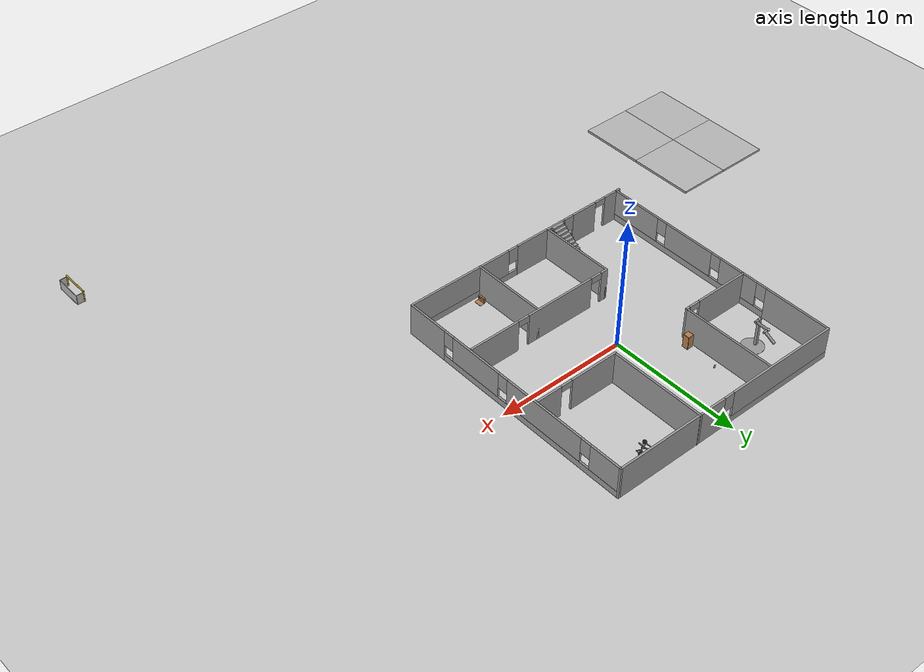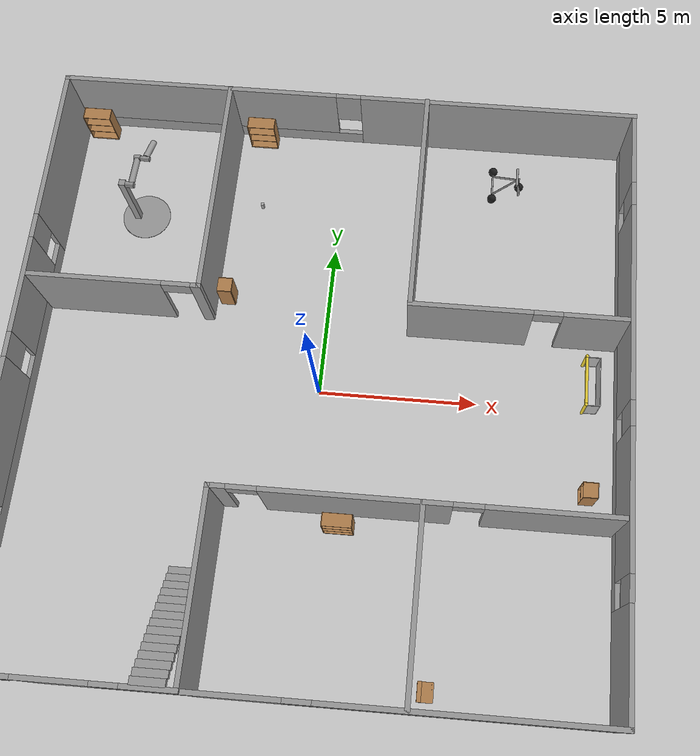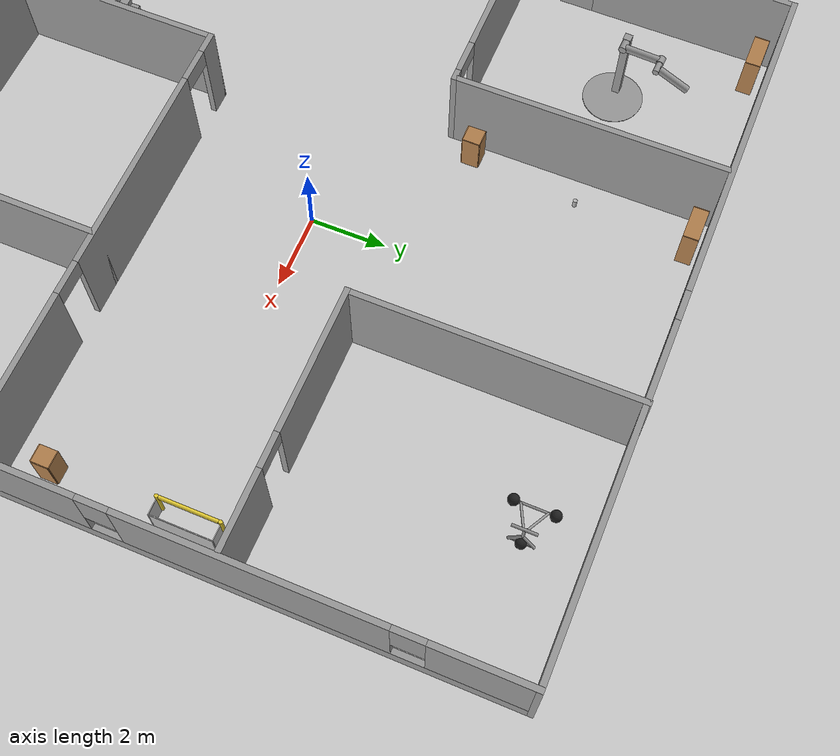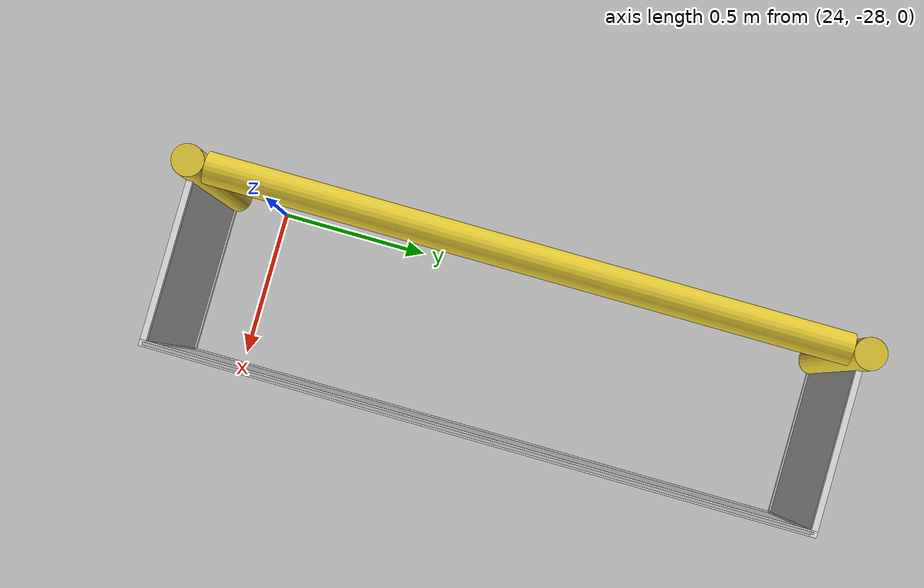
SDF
<sdf version="1.7">
 <world name="default">
  <light name="sun" type="directional">
   <pose>0 0 10 0 -0 0</pose>
   <diffuse>0.8 0.8 0.8 1</diffuse>
   <specular>0.2 0.2 0.2 1</specular>
   <attenuation>
    <range>1000</range>
    <constant>0.9</constant>
    <linear>0.01</linear>
    <quadratic>0.001</quadratic>
   </attenuation>
   <direction>-0.5 0.1 -0.9</direction>
   <spot><inner_angle>0</inner_angle><outer_angle>0</outer_angle><falloff>0</falloff></spot>
  </light>
  <model name="ground_plane">
   <static>1</static>
   <link name="link">
    <collision name="collision">
     <geometry><plane><normal>0 0 1</normal><size>100 100</size></plane></geometry>
     <surface><friction><ode><mu>100</mu><mu2>50</mu2></ode></friction></surface>
    </collision>
    <visual name="visual">
     <cast_shadows>0</cast_shadows>
     <geometry><plane><normal>0 0 1</normal><size>100 100</size></plane></geometry>
     <material>
      <script><uri>file://media/materials/scripts/gazebo.material</uri><name>Gazebo/Grey</name></script>
     </material>
    </visual>
   </link>
  </model>
  <gravity>0 0 -9.8</gravity>
  <magnetic_field>6e-06 2.3e-05 -4.2e-05</magnetic_field>
  <atmosphere type="adiabatic"/>
  <physics type="ode">
   <max_step_size>0.001</max_step_size>
   <real_time_factor>1</real_time_factor>
   <real_time_update_rate>1000</real_time_update_rate>
  </physics>
  <scene><ambient>0.4 0.4 0.4 1</ambient><background>0.7 0.7 0.7 1</background><shadows>1</shadows></scene>
  <spherical_coordinates>
   <surface_model>EARTH_WGS84</surface_model>
   <latitude_deg>0</latitude_deg>
   <longitude_deg>0</longitude_deg>
   <elevation>0</elevation>
   <heading_deg>0</heading_deg>
  </spherical_coordinates>
  <model name="tony_house.world">
   <pose>0.003919 0.011841 0 0 -0 0</pose>
   <link name="Stairs_0">
    <visual name="Stairs_0_Visual_0">
     <pose>-3.39052 -5.99335 0.083333 0 -0 0</pose>
     <geometry><box><size>1 0.233333 0.166667</size></box></geometry>
     <material>
      <script><uri>file://media/materials/scripts/gazebo.material</uri><name>Gazebo/Grey</name></script>
      <ambient>1 1 1 1</ambient>
     </material>
     <meta><layer>0</layer></meta>
    </visual>
    <collision name="Stairs_0_Collision_0">
     <geometry><box><size>1 0.233333 0.166667</size></box></geometry>
     <pose>-3.39052 -5.99335 0.083333 0 -0 0</pose>
    </collision>
    <visual name="Stairs_0_Visual_1">
     <pose>-3.39052 -6.22668 0.25 0 -0 0</pose>
     <geometry><box><size>1 0.233333 0.166667</size></box></geometry>
     <material>
      <script><uri>file://media/materials/scripts/gazebo.material</uri><name>Gazebo/Grey</name></script>
      <ambient>1 1 1 1</ambient>
     </material>
     <meta><layer>0</layer></meta>
    </visual>
    <collision name="Stairs_0_Collision_1">
     <geometry><box><size>1 0.233333 0.166667</size></box></geometry>
     <pose>-3.39052 -6.22668 0.25 0 -0 0</pose>
    </collision>
    <visual name="Stairs_0_Visual_2">
     <pose>-3.39052 -6.46001 0.416667 0 -0 0</pose>
     <geometry><box><size>1 0.233333 0.166667</size></box></geometry>
     <material>
      <script><uri>file://media/materials/scripts/gazebo.material</uri><name>Gazebo/Grey</name></script>
      <ambient>1 1 1 1</ambient>
     </material>
     <meta><layer>0</layer></meta>
    </visual>
    <collision name="Stairs_0_Collision_2">
     <geometry><box><size>1 0.233333 0.166667</size></box></geometry>
     <pose>-3.39052 -6.46001 0.416667 0 -0 0</pose>
    </collision>
    <visual name="Stairs_0_Visual_3">
     <pose>-3.39052 -6.69335 0.583333 0 -0 0</pose>
     <geometry><box><size>1 0.233333 0.166667</size></box></geometry>
     <material>
      <script><uri>file://media/materials/scripts/gazebo.material</uri><name>Gazebo/Grey</name></script>
      <ambient>1 1 1 1</ambient>
     </material>
     <meta><layer>0</layer></meta>
    </visual>
    <collision name="Stairs_0_Collision_3">
     <geometry><box><size>1 0.233333 0.166667</size></box></geometry>
     <pose>-3.39052 -6.69335 0.583333 0 -0 0</pose>
    </collision>
    <visual name="Stairs_0_Visual_4">
     <pose>-3.39052 -6.92668 0.75 0 -0 0</pose>
     <geometry><box><size>1 0.233333 0.166667</size></box></geometry>
     <material>
      <script><uri>file://media/materials/scripts/gazebo.material</uri><name>Gazebo/Grey</name></script>
      <ambient>1 1 1 1</ambient>
     </material>
     <meta><layer>0</layer></meta>
    </visual>
    <collision name="Stairs_0_Collision_4">
     <geometry><box><size>1 0.233333 0.166667</size></box></geometry>
     <pose>-3.39052 -6.92668 0.75 0 -0 0</pose>
    </collision>
    <visual name="Stairs_0_Visual_5">
     <pose>-3.39052 -7.16001 0.916667 0 -0 0</pose>
     <geometry><box><size>1 0.233333 0.166667</size></box></geometry>
     <material>
      <script><uri>file://media/materials/scripts/gazebo.material</uri><name>Gazebo/Grey</name></script>
      <ambient>1 1 1 1</ambient>
     </material>
     <meta><layer>0</layer></meta>
    </visual>
    <collision name="Stairs_0_Collision_5">
     <geometry><box><size>1 0.233333 0.166667</size></box></geometry>
     <pose>-3.39052 -7.16001 0.916667 0 -0 0</pose>
    </collision>
    <visual name="Stairs_0_Visual_6">
     <pose>-3.39052 -7.39335 1.08333 0 -0 0</pose>
     <geometry><box><size>1 0.233333 0.166667</size></box></geometry>
     <material>
      <script><uri>file://media/materials/scripts/gazebo.material</uri><name>Gazebo/Grey</name></script>
      <ambient>1 1 1 1</ambient>
     </material>
     <meta><layer>0</layer></meta>
    </visual>
    <collision name="Stairs_0_Collision_6">
     <geometry><box><size>1 0.233333 0.166667</size></box></geometry>
     <pose>-3.39052 -7.39335 1.08333 0 -0 0</pose>
    </collision>
    <visual name="Stairs_0_Visual_7">
     <pose>-3.39052 -7.62668 1.25 0 -0 0</pose>
     <geometry><box><size>1 0.233333 0.166667</size></box></geometry>
     <material>
      <script><uri>file://media/materials/scripts/gazebo.material</uri><name>Gazebo/Grey</name></script>
      <ambient>1 1 1 1</ambient>
     </material>
     <meta><layer>0</layer></meta>
    </visual>
    <collision name="Stairs_0_Collision_7">
     <geometry><box><size>1 0.233333 0.166667</size></box></geometry>
     <pose>-3.39052 -7.62668 1.25 0 -0 0</pose>
    </collision>
    <visual name="Stairs_0_Visual_8">
     <pose>-3.39052 -7.86001 1.41667 0 -0 0</pose>
     <geometry><box><size>1 0.233333 0.166667</size></box></geometry>
     <material>
      <script><uri>file://media/materials/scripts/gazebo.material</uri><name>Gazebo/Grey</name></script>
      <ambient>1 1 1 1</ambient>
     </material>
     <meta><layer>0</layer></meta>
    </visual>
    <collision name="Stairs_0_Collision_8">
     <geometry><box><size>1 0.233333 0.166667</size></box></geometry>
     <pose>-3.39052 -7.86001 1.41667 0 -0 0</pose>
    </collision>
    <visual name="Stairs_0_Visual_9">
     <pose>-3.39052 -8.09335 1.58333 0 -0 0</pose>
     <geometry><box><size>1 0.233333 0.166667</size></box></geometry>
     <material>
      <script><uri>file://media/materials/scripts/gazebo.material</uri><name>Gazebo/Grey</name></script>
      <ambient>1 1 1 1</ambient>
     </material>
     <meta><layer>0</layer></meta>
    </visual>
    <collision name="Stairs_0_Collision_9">
     <geometry><box><size>1 0.233333 0.166667</size></box></geometry>
     <pose>-3.39052 -8.09335 1.58333 0 -0 0</pose>
    </collision>
    <visual name="Stairs_0_Visual_10">
     <pose>-3.39052 -8.32668 1.75 0 -0 0</pose>
     <geometry><box><size>1 0.233333 0.166667</size></box></geometry>
     <material>
      <script><uri>file://media/materials/scripts/gazebo.material</uri><name>Gazebo/Grey</name></script>
      <ambient>1 1 1 1</ambient>
     </material>
     <meta><layer>0</layer></meta>
    </visual>
    <collision name="Stairs_0_Collision_10">
     <geometry><box><size>1 0.233333 0.166667</size></box></geometry>
     <pose>-3.39052 -8.32668 1.75 0 -0 0</pose>
    </collision>
    <visual name="Stairs_0_Visual_11">
     <pose>-3.39052 -8.56001 1.91667 0 -0 0</pose>
     <geometry><box><size>1 0.233333 0.166667</size></box></geometry>
     <material>
      <script><uri>file://media/materials/scripts/gazebo.material</uri><name>Gazebo/Grey</name></script>
      <ambient>1 1 1 1</ambient>
     </material>
     <meta><layer>0</layer></meta>
    </visual>
    <collision name="Stairs_0_Collision_11">
     <geometry><box><size>1 0.233333 0.166667</size></box></geometry>
     <pose>-3.39052 -8.56001 1.91667 0 -0 0</pose>
    </collision>
    <visual name="Stairs_0_Visual_12">
     <pose>-3.39052 -8.79335 2.08333 0 -0 0</pose>
     <geometry><box><size>1 0.233333 0.166667</size></box></geometry>
     <material>
      <script><uri>file://media/materials/scripts/gazebo.material</uri><name>Gazebo/Grey</name></script>
      <ambient>1 1 1 1</ambient>
     </material>
     <meta><layer>0</layer></meta>
    </visual>
    <collision name="Stairs_0_Collision_12">
     <geometry><box><size>1 0.233333 0.166667</size></box></geometry>
     <pose>-3.39052 -8.79335 2.08333 0 -0 0</pose>
    </collision>
    <visual name="Stairs_0_Visual_13">
     <pose>-3.39052 -9.02668 2.25 0 -0 0</pose>
     <geometry><box><size>1 0.233333 0.166667</size></box></geometry>
     <material>
      <script><uri>file://media/materials/scripts/gazebo.material</uri><name>Gazebo/Grey</name></script>
      <ambient>1 1 1 1</ambient>
     </material>
     <meta><layer>0</layer></meta>
    </visual>
    <collision name="Stairs_0_Collision_13">
     <geometry><box><size>1 0.233333 0.166667</size></box></geometry>
     <pose>-3.39052 -9.02668 2.25 0 -0 0</pose>
    </collision>
    <visual name="Stairs_0_Visual_14">
     <pose>-3.39052 -9.26001 2.41667 0 -0 0</pose>
     <geometry><box><size>1 0.233333 0.166667</size></box></geometry>
     <material>
      <script><uri>file://media/materials/scripts/gazebo.material</uri><name>Gazebo/Grey</name></script>
      <ambient>1 1 1 1</ambient>
     </material>
     <meta><layer>0</layer></meta>
    </visual>
    <collision name="Stairs_0_Collision_14">
     <geometry><box><size>1 0.233333 0.166667</size></box></geometry>
     <pose>-3.39052 -9.26001 2.41667 0 -0 0</pose>
    </collision>
   </link>
   <link name="Wall_1">
    <pose>-6.01156 -9.43056 0 0 -0 0.001171</pose>
    <visual name="Wall_1_Visual_0">
     <pose>-2.72986 0 1.25 0 -0 0</pose>
     <geometry><box><size>1.51416 0.15 2.5</size></box></geometry>
     <material>
      <script><uri>file://media/materials/scripts/gazebo.material</uri><name>Gazebo/Grey</name></script>
      <ambient>1 1 1 1</ambient>
     </material>
     <meta><layer>0</layer></meta>
    </visual>
    <collision name="Wall_1_Collision_0">
     <geometry><box><size>1.51416 0.15 2.5</size></box></geometry>
     <pose>-2.72986 0 1.25 0 -0 0</pose>
    </collision>
    <visual name="Wall_1_Visual_1">
     <pose>-0.004916 0 1.25 0 -0 0</pose>
     <geometry><box><size>2.13573 0.15 2.5</size></box></geometry>
     <material>
      <script><uri>file://media/materials/scripts/gazebo.material</uri><name>Gazebo/Grey</name></script>
      <ambient>1 1 1 1</ambient>
     </material>
     <meta><layer>0</layer></meta>
    </visual>
    <collision name="Wall_1_Collision_1">
     <geometry><box><size>2.13573 0.15 2.5</size></box></geometry>
     <pose>-0.004916 0 1.25 0 -0 0</pose>
    </collision>
    <visual name="Wall_1_Visual_2">
     <pose>2.27494 0 0.25 0 -0 0</pose>
     <geometry><box><size>2.42399 0.15 0.5</size></box></geometry>
     <material>
      <script><uri>file://media/materials/scripts/gazebo.material</uri><name>Gazebo/Grey</name></script>
      <ambient>1 1 1 1</ambient>
     </material>
     <meta><layer>0</layer></meta>
    </visual>
    <collision name="Wall_1_Collision_2">
     <geometry><box><size>2.42399 0.15 0.5</size></box></geometry>
     <pose>2.27494 0 0.25 0 -0 0</pose>
    </collision>
    <visual name="Wall_1_Visual_3">
     <pose>2.67494 0 1.5 0 -0 0</pose>
     <geometry><box><size>1.62399 0.15 2</size></box></geometry>
     <material>
      <script><uri>file://media/materials/scripts/gazebo.material</uri><name>Gazebo/Grey</name></script>
      <ambient>1 1 1 1</ambient>
     </material>
     <meta><layer>0</layer></meta>
    </visual>
    <collision name="Wall_1_Collision_3">
     <geometry><box><size>1.62399 0.15 2</size></box></geometry>
     <pose>2.67494 0 1.5 0 -0 0</pose>
    </collision>
    <visual name="Wall_1_Visual_4">
     <pose>1.46295 0 1.9 0 -0 0</pose>
     <geometry><box><size>0.8 0.15 1.2</size></box></geometry>
     <material>
      <script><uri>file://media/materials/scripts/gazebo.material</uri><name>Gazebo/Grey</name></script>
      <ambient>1 1 1 1</ambient>
     </material>
     <meta><layer>0</layer></meta>
    </visual>
    <collision name="Wall_1_Collision_4">
     <geometry><box><size>0.8 0.15 1.2</size></box></geometry>
     <pose>1.46295 0 1.9 0 -0 0</pose>
    </collision>
    <visual name="Wall_1_Visual_5">
     <pose>-1.52278 0 2.25 0 -0 0</pose>
     <geometry><box><size>0.9 0.15 0.5</size></box></geometry>
     <material>
      <script><uri>file://media/materials/scripts/gazebo.material</uri><name>Gazebo/Grey</name></script>
      <ambient>1 1 1 1</ambient>
     </material>
     <meta><layer>0</layer></meta>
    </visual>
    <collision name="Wall_1_Collision_5">
     <geometry><box><size>0.9 0.15 0.5</size></box></geometry>
     <pose>-1.52278 0 2.25 0 -0 0</pose>
    </collision>
   </link>
   <link name="Wall_10">
    <pose>3.32538 -3.82656 0 0 -0 0</pose>
    <visual name="Wall_10_Visual_0">
     <pose>-5.70576 0 1.25 0 -0 0</pose>
     <geometry><box><size>0.588485 0.15 2.5</size></box></geometry>
     <material>
      <script><uri>file://media/materials/scripts/gazebo.material</uri><name>Gazebo/Grey</name></script>
      <ambient>1 1 1 1</ambient>
     </material>
     <meta><layer>0</layer></meta>
    </visual>
    <collision name="Wall_10_Collision_0">
     <geometry><box><size>0.588485 0.15 2.5</size></box></geometry>
     <pose>-5.70576 0 1.25 0 -0 0</pose>
    </collision>
    <visual name="Wall_10_Visual_1">
     <pose>-1.72323 0 1.25 0 -0 0</pose>
     <geometry><box><size>5.57657 0.15 2.5</size></box></geometry>
     <material>
      <script><uri>file://media/materials/scripts/gazebo.material</uri><name>Gazebo/Grey</name></script>
      <ambient>1 1 1 1</ambient>
     </material>
     <meta><layer>0</layer></meta>
    </visual>
    <collision name="Wall_10_Collision_1">
     <geometry><box><size>5.57657 0.15 2.5</size></box></geometry>
     <pose>-1.72323 0 1.25 0 -0 0</pose>
    </collision>
    <visual name="Wall_10_Visual_2">
     <pose>3.98253 0 1.25 0 -0 0</pose>
     <geometry><box><size>4.03494 0.15 2.5</size></box></geometry>
     <material>
      <script><uri>file://media/materials/scripts/gazebo.material</uri><name>Gazebo/Grey</name></script>
      <ambient>1 1 1 1</ambient>
     </material>
     <meta><layer>0</layer></meta>
    </visual>
    <collision name="Wall_10_Collision_2">
     <geometry><box><size>4.03494 0.15 2.5</size></box></geometry>
     <pose>3.98253 0 1.25 0 -0 0</pose>
    </collision>
    <visual name="Wall_10_Visual_3">
     <pose>-4.96152 0 2.25 0 -0 0</pose>
     <geometry><box><size>0.9 0.15 0.5</size></box></geometry>
     <material>
      <script><uri>file://media/materials/scripts/gazebo.material</uri><name>Gazebo/Grey</name></script>
      <ambient>1 1 1 1</ambient>
     </material>
     <meta><layer>0</layer></meta>
    </visual>
    <collision name="Wall_10_Collision_3">
     <geometry><box><size>0.9 0.15 0.5</size></box></geometry>
     <pose>-4.96152 0 2.25 0 -0 0</pose>
    </collision>
    <visual name="Wall_10_Visual_4">
     <pose>1.51506 0 2.25 0 -0 0</pose>
     <geometry><box><size>0.9 0.15 0.5</size></box></geometry>
     <material>
      <script><uri>file://media/materials/scripts/gazebo.material</uri><name>Gazebo/Grey</name></script>
      <ambient>1 1 1 1</ambient>
     </material>
     <meta><layer>0</layer></meta>
    </visual>
    <collision name="Wall_10_Collision_4">
     <geometry><box><size>0.9 0.15 0.5</size></box></geometry>
     <pose>1.51506 0 2.25 0 -0 0</pose>
    </collision>
   </link>
   <link name="Wall_12">
    <collision name="Wall_12_Collision">
     <geometry><box><size>5.75 0.15 2.5</size></box></geometry>
     <pose>0 0 1.25 0 -0 0</pose>
    </collision>
    <visual name="Wall_12_Visual">
     <pose>0 0 1.25 0 -0 0</pose>
     <geometry><box><size>5.75 0.15 2.5</size></box></geometry>
     <material>
      <script><uri>file://media/materials/scripts/gazebo.material</uri><name>Gazebo/Grey</name></script>
      <ambient>1 1 1 1</ambient>
     </material>
     <meta><layer>0</layer></meta>
    </visual>
    <pose>3.54453 -6.62656 0 0 -0 -1.5708</pose>
   </link>
   <link name="Wall_14">
    <pose>5.98556 2.23237 0 0 -0 0</pose>
    <visual name="Wall_14_Visual_0">
     <pose>-1.46444 0 1.25 0 -0 0</pose>
     <geometry><box><size>3.82112 0.15 2.5</size></box></geometry>
     <material>
      <script><uri>file://media/materials/scripts/gazebo.material</uri><name>Gazebo/Grey</name></script>
      <ambient>1 1 1 1</ambient>
     </material>
     <meta><layer>0</layer></meta>
    </visual>
    <collision name="Wall_14_Collision_0">
     <geometry><box><size>3.82112 0.15 2.5</size></box></geometry>
     <pose>-1.46444 0 1.25 0 -0 0</pose>
    </collision>
    <visual name="Wall_14_Visual_1">
     <pose>2.36056 0 1.25 0 -0 0</pose>
     <geometry><box><size>2.02888 0.15 2.5</size></box></geometry>
     <material>
      <script><uri>file://media/materials/scripts/gazebo.material</uri><name>Gazebo/Grey</name></script>
      <ambient>1 1 1 1</ambient>
     </material>
     <meta><layer>0</layer></meta>
    </visual>
    <collision name="Wall_14_Collision_1">
     <geometry><box><size>2.02888 0.15 2.5</size></box></geometry>
     <pose>2.36056 0 1.25 0 -0 0</pose>
    </collision>
    <visual name="Wall_14_Visual_2">
     <pose>0.896121 0 2.25 0 -0 0</pose>
     <geometry><box><size>0.9 0.15 0.5</size></box></geometry>
     <material>
      <script><uri>file://media/materials/scripts/gazebo.material</uri><name>Gazebo/Grey</name></script>
      <ambient>1 1 1 1</ambient>
     </material>
     <meta><layer>0</layer></meta>
    </visual>
    <collision name="Wall_14_Collision_2">
     <geometry><box><size>0.9 0.15 0.5</size></box></geometry>
     <pose>0.896121 0 2.25 0 -0 0</pose>
    </collision>
   </link>
   <link name="Wall_18">
    <collision name="Wall_18_Collision">
     <geometry><box><size>7.25 0.15 2.5</size></box></geometry>
     <pose>0 0 1.25 0 -0 0</pose>
    </collision>
    <visual name="Wall_18_Visual">
     <pose>0 0 1.25 0 -0 0</pose>
     <geometry><box><size>7.25 0.15 2.5</size></box></geometry>
     <material>
      <script><uri>file://media/materials/scripts/gazebo.material</uri><name>Gazebo/Grey</name></script>
      <ambient>1 1 1 1</ambient>
     </material>
     <meta><layer>0</layer></meta>
    </visual>
    <pose>-3.77724 5.84349 0 0 -0 -1.5708</pose>
   </link>
   <link name="Wall_20">
    <collision name="Wall_20_Collision">
     <geometry><box><size>7.25 0.15 2.5</size></box></geometry>
     <pose>0 0 1.25 0 -0 0</pose>
    </collision>
    <visual name="Wall_20_Visual">
     <pose>0 0 1.25 0 -0 0</pose>
     <geometry><box><size>7.25 0.15 2.5</size></box></geometry>
     <material>
      <script><uri>file://media/materials/scripts/gazebo.material</uri><name>Gazebo/Grey</name></script>
      <ambient>1 1 1 1</ambient>
     </material>
     <meta><layer>0</layer></meta>
    </visual>
    <pose>2.68958 5.89002 0 0 -0 -1.5708</pose>
   </link>
   <link name="Wall_22">
    <pose>-6.45224 2.29349 0 0 -0 3.14159</pose>
    <visual name="Wall_22_Visual_0">
     <pose>-2.58857 0 1.25 0 -0 0</pose>
     <geometry><box><size>0.322859 0.15 2.5</size></box></geometry>
     <material>
      <script><uri>file://media/materials/scripts/gazebo.material</uri><name>Gazebo/Grey</name></script>
      <ambient>1 1 1 1</ambient>
     </material>
     <meta><layer>0</layer></meta>
    </visual>
    <collision name="Wall_22_Collision_0">
     <geometry><box><size>0.322859 0.15 2.5</size></box></geometry>
     <pose>-2.58857 0 1.25 0 -0 0</pose>
    </collision>
    <visual name="Wall_22_Visual_1">
     <pose>0.611429 0 1.25 0 -0 0</pose>
     <geometry><box><size>4.27714 0.15 2.5</size></box></geometry>
     <material>
      <script><uri>file://media/materials/scripts/gazebo.material</uri><name>Gazebo/Grey</name></script>
      <ambient>1 1 1 1</ambient>
     </material>
     <meta><layer>0</layer></meta>
    </visual>
    <collision name="Wall_22_Collision_1">
     <geometry><box><size>4.27714 0.15 2.5</size></box></geometry>
     <pose>0.611429 0 1.25 0 -0 0</pose>
    </collision>
    <visual name="Wall_22_Visual_2">
     <pose>-1.97714 0 2.25 0 -0 0</pose>
     <geometry><box><size>0.9 0.15 0.5</size></box></geometry>
     <material>
      <script><uri>file://media/materials/scripts/gazebo.material</uri><name>Gazebo/Grey</name></script>
      <ambient>1 1 1 1</ambient>
     </material>
     <meta><layer>0</layer></meta>
    </visual>
    <collision name="Wall_22_Collision_2">
     <geometry><box><size>0.9 0.15 0.5</size></box></geometry>
     <pose>-1.97714 0 2.25 0 -0 0</pose>
    </collision>
   </link>
   <link name="Wall_24">
    <collision name="Wall_24_Collision">
     <geometry><box><size>5.75 0.15 2.5</size></box></geometry>
     <pose>0 0 1.25 0 -0 0</pose>
    </collision>
    <visual name="Wall_24_Visual">
     <pose>0 0 1.25 0 -0 0</pose>
     <geometry><box><size>5.75 0.15 2.5</size></box></geometry>
     <material>
      <script><uri>file://media/materials/scripts/gazebo.material</uri><name>Gazebo/Grey</name></script>
      <ambient>1 1 1 1</ambient>
     </material>
     <meta><layer>0</layer></meta>
    </visual>
    <pose>-2.59962 -6.62656 0 0 -0 -1.5708</pose>
   </link>
   <link name="Wall_3">
    <pose>3.49858 -9.44002 0 0 -0 0</pose>
    <visual name="Wall_3_Visual_0">
     <pose>-4.64469 0 1.25 0 -0 0</pose>
     <geometry><box><size>2.71062 0.15 2.5</size></box></geometry>
     <material>
      <script><uri>file://media/materials/scripts/gazebo.material</uri><name>Gazebo/Grey</name></script>
      <ambient>1 1 1 1</ambient>
     </material>
     <meta><layer>0</layer></meta>
    </visual>
    <collision name="Wall_3_Collision_0">
     <geometry><box><size>2.71062 0.15 2.5</size></box></geometry>
     <pose>-4.64469 0 1.25 0 -0 0</pose>
    </collision>
    <visual name="Wall_3_Visual_1">
     <pose>1.35531 0 0.25 0 -0 0</pose>
     <geometry><box><size>9.28938 0.15 0.5</size></box></geometry>
     <material>
      <script><uri>file://media/materials/scripts/gazebo.material</uri><name>Gazebo/Grey</name></script>
      <ambient>1 1 1 1</ambient>
     </material>
     <meta><layer>0</layer></meta>
    </visual>
    <collision name="Wall_3_Collision_1">
     <geometry><box><size>9.28938 0.15 0.5</size></box></geometry>
     <pose>1.35531 0 0.25 0 -0 0</pose>
    </collision>
    <visual name="Wall_3_Visual_2">
     <pose>1.75531 0 1.5 0 -0 0</pose>
     <geometry><box><size>8.48938 0.15 2</size></box></geometry>
     <material>
      <script><uri>file://media/materials/scripts/gazebo.material</uri><name>Gazebo/Grey</name></script>
      <ambient>1 1 1 1</ambient>
     </material>
     <meta><layer>0</layer></meta>
    </visual>
    <collision name="Wall_3_Collision_2">
     <geometry><box><size>8.48938 0.15 2</size></box></geometry>
     <pose>1.75531 0 1.5 0 -0 0</pose>
    </collision>
    <visual name="Wall_3_Visual_3">
     <pose>-2.88938 0 1.9 0 -0 0</pose>
     <geometry><box><size>0.8 0.15 1.2</size></box></geometry>
     <material>
      <script><uri>file://media/materials/scripts/gazebo.material</uri><name>Gazebo/Grey</name></script>
      <ambient>1 1 1 1</ambient>
     </material>
     <meta><layer>0</layer></meta>
    </visual>
    <collision name="Wall_3_Collision_3">
     <geometry><box><size>0.8 0.15 1.2</size></box></geometry>
     <pose>-2.88938 0 1.9 0 -0 0</pose>
    </collision>
   </link>
   <link name="Wall_4">
    <pose>9.42358 -0.015016 0 0 -0 1.5708</pose>
    <visual name="Wall_4_Visual_0">
     <pose>-7.8218 0 1.25 0 -0 0</pose>
     <geometry><box><size>3.3564 0.15 2.5</size></box></geometry>
     <material>
      <script><uri>file://media/materials/scripts/gazebo.material</uri><name>Gazebo/Grey</name></script>
      <ambient>1 1 1 1</ambient>
     </material>
     <meta><layer>0</layer></meta>
    </visual>
    <collision name="Wall_4_Collision_0">
     <geometry><box><size>3.3564 0.15 2.5</size></box></geometry>
     <pose>-7.8218 0 1.25 0 -0 0</pose>
    </collision>
    <visual name="Wall_4_Visual_1">
     <pose>1.6782 0 0.25 0 -0 0</pose>
     <geometry><box><size>15.6436 0.15 0.5</size></box></geometry>
     <material>
      <script><uri>file://media/materials/scripts/gazebo.material</uri><name>Gazebo/Grey</name></script>
      <ambient>1 1 1 1</ambient>
     </material>
     <meta><layer>0</layer></meta>
    </visual>
    <collision name="Wall_4_Collision_1">
     <geometry><box><size>15.6436 0.15 0.5</size></box></geometry>
     <pose>1.6782 0 0.25 0 -0 0</pose>
    </collision>
    <visual name="Wall_4_Visual_2">
     <pose>-3.21561 0 1.5 0 -0 0</pose>
     <geometry><box><size>4.25599 0.15 2</size></box></geometry>
     <material>
      <script><uri>file://media/materials/scripts/gazebo.material</uri><name>Gazebo/Grey</name></script>
      <ambient>1 1 1 1</ambient>
     </material>
     <meta><layer>0</layer></meta>
    </visual>
    <collision name="Wall_4_Collision_2">
     <geometry><box><size>4.25599 0.15 2</size></box></geometry>
     <pose>-3.21561 0 1.5 0 -0 0</pose>
    </collision>
    <visual name="Wall_4_Visual_3">
     <pose>2.94431 0 1.5 0 -0 0</pose>
     <geometry><box><size>6.46384 0.15 2</size></box></geometry>
     <material>
      <script><uri>file://media/materials/scripts/gazebo.material</uri><name>Gazebo/Grey</name></script>
      <ambient>1 1 1 1</ambient>
     </material>
     <meta><layer>0</layer></meta>
    </visual>
    <collision name="Wall_4_Collision_3">
     <geometry><box><size>6.46384 0.15 2</size></box></geometry>
     <pose>2.94431 0 1.5 0 -0 0</pose>
    </collision>
    <visual name="Wall_4_Visual_4">
     <pose>8.23811 0 1.5 0 -0 0</pose>
     <geometry><box><size>2.52377 0.15 2</size></box></geometry>
     <material>
      <script><uri>file://media/materials/scripts/gazebo.material</uri><name>Gazebo/Grey</name></script>
      <ambient>1 1 1 1</ambient>
     </material>
     <meta><layer>0</layer></meta>
    </visual>
    <collision name="Wall_4_Collision_4">
     <geometry><box><size>2.52377 0.15 2</size></box></geometry>
     <pose>8.23811 0 1.5 0 -0 0</pose>
    </collision>
    <visual name="Wall_4_Visual_5">
     <pose>-5.7436 0 1.9 0 -0 0</pose>
     <geometry><box><size>0.8 0.15 1.2</size></box></geometry>
     <material>
      <script><uri>file://media/materials/scripts/gazebo.material</uri><name>Gazebo/Grey</name></script>
      <ambient>1 1 1 1</ambient>
     </material>
     <meta><layer>0</layer></meta>
    </visual>
    <collision name="Wall_4_Collision_5">
     <geometry><box><size>0.8 0.15 1.2</size></box></geometry>
     <pose>-5.7436 0 1.9 0 -0 0</pose>
    </collision>
    <visual name="Wall_4_Visual_6">
     <pose>-0.687612 0 1.9 0 -0 0</pose>
     <geometry><box><size>0.8 0.15 1.2</size></box></geometry>
     <material>
      <script><uri>file://media/materials/scripts/gazebo.material</uri><name>Gazebo/Grey</name></script>
      <ambient>1 1 1 1</ambient>
     </material>
     <meta><layer>0</layer></meta>
    </visual>
    <collision name="Wall_4_Collision_6">
     <geometry><box><size>0.8 0.15 1.2</size></box></geometry>
     <pose>-0.687612 0 1.9 0 -0 0</pose>
    </collision>
    <visual name="Wall_4_Visual_7">
     <pose>6.57623 0 1.9 0 -0 0</pose>
     <geometry><box><size>0.8 0.15 1.2</size></box></geometry>
     <material>
      <script><uri>file://media/materials/scripts/gazebo.material</uri><name>Gazebo/Grey</name></script>
      <ambient>1 1 1 1</ambient>
     </material>
     <meta><layer>0</layer></meta>
    </visual>
    <collision name="Wall_4_Collision_7">
     <geometry><box><size>0.8 0.15 1.2</size></box></geometry>
     <pose>6.57623 0 1.9 0 -0 0</pose>
    </collision>
   </link>
   <link name="Wall_5">
    <pose>0.123583 9.40998 0 0 -0 3.14159</pose>
    <visual name="Wall_5_Visual_0">
     <pose>-4.87823 0 1.25 0 -0 0</pose>
     <geometry><box><size>8.99354 0.15 2.5</size></box></geometry>
     <material>
      <script><uri>file://media/materials/scripts/gazebo.material</uri><name>Gazebo/Grey</name></script>
      <ambient>1 1 1 1</ambient>
     </material>
     <meta><layer>0</layer></meta>
    </visual>
    <collision name="Wall_5_Collision_0">
     <geometry><box><size>8.99354 0.15 2.5</size></box></geometry>
     <pose>-4.87823 0 1.25 0 -0 0</pose>
    </collision>
    <visual name="Wall_5_Visual_1">
     <pose>4.49677 0 0.25 0 -0 0</pose>
     <geometry><box><size>9.75646 0.15 0.5</size></box></geometry>
     <material>
      <script><uri>file://media/materials/scripts/gazebo.material</uri><name>Gazebo/Grey</name></script>
      <ambient>1 1 1 1</ambient>
     </material>
     <meta><layer>0</layer></meta>
    </visual>
    <collision name="Wall_5_Collision_1">
     <geometry><box><size>9.75646 0.15 0.5</size></box></geometry>
     <pose>4.49677 0 0.25 0 -0 0</pose>
    </collision>
    <visual name="Wall_5_Visual_2">
     <pose>4.89677 0 1.5 0 -0 0</pose>
     <geometry><box><size>8.95646 0.15 2</size></box></geometry>
     <material>
      <script><uri>file://media/materials/scripts/gazebo.material</uri><name>Gazebo/Grey</name></script>
      <ambient>1 1 1 1</ambient>
     </material>
     <meta><layer>0</layer></meta>
    </visual>
    <collision name="Wall_5_Collision_2">
     <geometry><box><size>8.95646 0.15 2</size></box></geometry>
     <pose>4.89677 0 1.5 0 -0 0</pose>
    </collision>
    <visual name="Wall_5_Visual_3">
     <pose>0.018538 0 1.9 0 -0 0</pose>
     <geometry><box><size>0.8 0.15 1.2</size></box></geometry>
     <material>
      <script><uri>file://media/materials/scripts/gazebo.material</uri><name>Gazebo/Grey</name></script>
      <ambient>1 1 1 1</ambient>
     </material>
     <meta><layer>0</layer></meta>
    </visual>
    <collision name="Wall_5_Collision_3">
     <geometry><box><size>0.8 0.15 1.2</size></box></geometry>
     <pose>0.018538 0 1.9 0 -0 0</pose>
    </collision>
   </link>
   <link name="Wall_6">
    <pose>-9.17642 -0.015016 0 0 -0 -1.5708</pose>
    <visual name="Wall_6_Visual_0">
     <pose>-6.9156 0 1.25 0 -0 0</pose>
     <geometry><box><size>5.1688 0.15 2.5</size></box></geometry>
     <material>
      <script><uri>file://media/materials/scripts/gazebo.material</uri><name>Gazebo/Grey</name></script>
      <ambient>1 1 1 1</ambient>
     </material>
     <meta><layer>0</layer></meta>
    </visual>
    <collision name="Wall_6_Collision_0">
     <geometry><box><size>5.1688 0.15 2.5</size></box></geometry>
     <pose>-6.9156 0 1.25 0 -0 0</pose>
    </collision>
    <visual name="Wall_6_Visual_1">
     <pose>2.5844 0 0.25 0 -0 0</pose>
     <geometry><box><size>13.8312 0.15 0.5</size></box></geometry>
     <material>
      <script><uri>file://media/materials/scripts/gazebo.material</uri><name>Gazebo/Grey</name></script>
      <ambient>1 1 1 1</ambient>
     </material>
     <meta><layer>0</layer></meta>
    </visual>
    <collision name="Wall_6_Collision_1">
     <geometry><box><size>13.8312 0.15 0.5</size></box></geometry>
     <pose>2.5844 0 0.25 0 -0 0</pose>
    </collision>
    <visual name="Wall_6_Visual_2">
     <pose>-1.94373 0 1.5 0 -0 0</pose>
     <geometry><box><size>3.17493 0.15 2</size></box></geometry>
     <material>
      <script><uri>file://media/materials/scripts/gazebo.material</uri><name>Gazebo/Grey</name></script>
      <ambient>1 1 1 1</ambient>
     </material>
     <meta><layer>0</layer></meta>
    </visual>
    <collision name="Wall_6_Collision_2">
     <geometry><box><size>3.17493 0.15 2</size></box></geometry>
     <pose>-1.94373 0 1.5 0 -0 0</pose>
    </collision>
    <visual name="Wall_6_Visual_3">
     <pose>2.50201 0 1.5 0 -0 0</pose>
     <geometry><box><size>4.11655 0.15 2</size></box></geometry>
     <material>
      <script><uri>file://media/materials/scripts/gazebo.material</uri><name>Gazebo/Grey</name></script>
      <ambient>1 1 1 1</ambient>
     </material>
     <meta><layer>0</layer></meta>
    </visual>
    <collision name="Wall_6_Collision_3">
     <geometry><box><size>4.11655 0.15 2</size></box></geometry>
     <pose>2.50201 0 1.5 0 -0 0</pose>
    </collision>
    <visual name="Wall_6_Visual_4">
     <pose>7.43014 0 1.5 0 -0 0</pose>
     <geometry><box><size>4.13971 0.15 2</size></box></geometry>
     <material>
      <script><uri>file://media/materials/scripts/gazebo.material</uri><name>Gazebo/Grey</name></script>
      <ambient>1 1 1 1</ambient>
     </material>
     <meta><layer>0</layer></meta>
    </visual>
    <collision name="Wall_6_Collision_4">
     <geometry><box><size>4.13971 0.15 2</size></box></geometry>
     <pose>7.43014 0 1.5 0 -0 0</pose>
    </collision>
    <visual name="Wall_6_Visual_5">
     <pose>-3.9312 0 1.9 0 -0 0</pose>
     <geometry><box><size>0.8 0.15 1.2</size></box></geometry>
     <material>
      <script><uri>file://media/materials/scripts/gazebo.material</uri><name>Gazebo/Grey</name></script>
      <ambient>1 1 1 1</ambient>
     </material>
     <meta><layer>0</layer></meta>
    </visual>
    <collision name="Wall_6_Collision_5">
     <geometry><box><size>0.8 0.15 1.2</size></box></geometry>
     <pose>-3.9312 0 1.9 0 -0 0</pose>
    </collision>
    <visual name="Wall_6_Visual_6">
     <pose>0.043735 0 1.9 0 -0 0</pose>
     <geometry><box><size>0.8 0.15 1.2</size></box></geometry>
     <material>
      <script><uri>file://media/materials/scripts/gazebo.material</uri><name>Gazebo/Grey</name></script>
      <ambient>1 1 1 1</ambient>
     </material>
     <meta><layer>0</layer></meta>
    </visual>
    <collision name="Wall_6_Collision_6">
     <geometry><box><size>0.8 0.15 1.2</size></box></geometry>
     <pose>0.043735 0 1.9 0 -0 0</pose>
    </collision>
    <visual name="Wall_6_Visual_7">
     <pose>4.96028 0 1.9 0 -0 0</pose>
     <geometry><box><size>0.8 0.15 1.2</size></box></geometry>
     <material>
      <script><uri>file://media/materials/scripts/gazebo.material</uri><name>Gazebo/Grey</name></script>
      <ambient>1 1 1 1</ambient>
     </material>
     <meta><layer>0</layer></meta>
    </visual>
    <collision name="Wall_6_Collision_7">
     <geometry><box><size>0.8 0.15 1.2</size></box></geometry>
     <pose>4.96028 0 1.9 0 -0 0</pose>
    </collision>
   </link>
   <static>1</static>
  </model>
  <model name="bookshelf">
   <static>1</static>
   <link name="link">
    <inertial><mass>1</mass></inertial>
    <collision name="back">
     <pose>0 0.005 0.6 0 -0 0</pose>
     <geometry><box><size>0.9 0.01 1.2</size></box></geometry>
    </collision>
    <visual name="visual1">
     <pose>0 0.005 0.6 0 -0 0</pose>
     <geometry><box><size>0.9 0.01 1.2</size></box></geometry>
     <material>
      <script><uri>file://media/materials/scripts/gazebo.material</uri><name>Gazebo/Wood</name></script>
     </material>
    </visual>
    <collision name="left_side">
     <pose>0.45 -0.195 0.6 0 -0 0</pose>
     <geometry><box><size>0.02 0.4 1.2</size></box></geometry>
    </collision>
    <visual name="visual2">
     <pose>0.45 -0.195 0.6 0 -0 0</pose>
     <geometry><box><size>0.02 0.4 1.2</size></box></geometry>
     <material>
      <script><uri>file://media/materials/scripts/gazebo.material</uri><name>Gazebo/Wood</name></script>
     </material>
    </visual>
    <collision name="right_side">
     <pose>-0.45 -0.195 0.6 0 -0 0</pose>
     <geometry><box><size>0.02 0.4 1.2</size></box></geometry>
    </collision>
    <visual name="visual3">
     <pose>-0.45 -0.195 0.6 0 -0 0</pose>
     <geometry><box><size>0.02 0.4 1.2</size></box></geometry>
     <material>
      <script><uri>file://media/materials/scripts/gazebo.material</uri><name>Gazebo/Wood</name></script>
     </material>
    </visual>
    <collision name="bottom">
     <pose>0 -0.195 0.03 0 -0 0</pose>
     <geometry><box><size>0.88 0.4 0.06</size></box></geometry>
    </collision>
    <visual name="visual4">
     <pose>0 -0.195 0.03 0 -0 0</pose>
     <geometry><box><size>0.88 0.4 0.06</size></box></geometry>
     <material>
      <script><uri>file://media/materials/scripts/gazebo.material</uri><name>Gazebo/Wood</name></script>
     </material>
    </visual>
    <collision name="top">
     <pose>0 -0.195 1.19 0 -0 0</pose>
     <geometry><box><size>0.88 0.4 0.02</size></box></geometry>
    </collision>
    <visual name="visual5">
     <pose>0 -0.195 1.19 0 -0 0</pose>
     <geometry><box><size>0.88 0.4 0.02</size></box></geometry>
     <material>
      <script><uri>file://media/materials/scripts/gazebo.material</uri><name>Gazebo/Wood</name></script>
     </material>
    </visual>
    <collision name="low_shelf">
     <pose>0 -0.195 0.43 0 -0 0</pose>
     <geometry><box><size>0.88 0.4 0.02</size></box></geometry>
    </collision>
    <visual name="visual6">
     <pose>0 -0.195 0.43 0 -0 0</pose>
     <geometry><box><size>0.88 0.4 0.02</size></box></geometry>
     <material>
      <script><uri>file://media/materials/scripts/gazebo.material</uri><name>Gazebo/Wood</name></script>
     </material>
    </visual>
    <collision name="high_shelf">
     <pose>0 -0.195 0.8 0 -0 0</pose>
     <geometry><box><size>0.88 0.4 0.02</size></box></geometry>
    </collision>
    <visual name="visual7">
     <pose>0 -0.195 0.8 0 -0 0</pose>
     <geometry><box><size>0.88 0.4 0.02</size></box></geometry>
     <material>
      <script><uri>file://media/materials/scripts/gazebo.material</uri><name>Gazebo/Wood</name></script>
     </material>
    </visual>
   </link>
   <pose>-2.88818 9.24085 0 0 -0 0</pose>
  </model>
  <model name="beer">
   <link name="link">
    <pose>0 0 0.115 0 -0 0</pose>
    <inertial>
     <mass>0.39</mass>
     <inertia><ixx>0.00058</ixx><ixy>0</ixy><ixz>0</ixz><iyy>0.00058</iyy><iyz>0</iyz><izz>0.00019</izz></inertia>
    </inertial>
    <collision name="collision">
     <geometry><cylinder><radius>0.055</radius><length>0.23</length></cylinder></geometry>
    </collision>
    <visual name="visual">
     <geometry><cylinder><radius>0.055</radius><length>0.23</length></cylinder></geometry>
     <material>
      <script>
       <uri>model://beer/materials/scripts</uri>
       <uri>model://beer/materials/textures</uri>
       <name>Beer/Diffuse</name>
      </script>
     </material>
    </visual>
   </link>
   <pose>-2.49538 6.08028 0.775001 1e-06 -2.7e-05 0.004211</pose>
  </model>
  <model name="cabinet">
   <static>1</static>
   <link name="cabinet_bottom_plate">
    <inertial>
     <pose>0 0 -1 0 -0 0</pose>
     <inertia><ixx>2.05</ixx><ixy>0</ixy><ixz>0</ixz><iyy>2.05</iyy><iyz>0</iyz><izz>2.05</izz></inertia>
     <mass>25</mass>
    </inertial>
    <collision name="cabinet_bottom_plate_geom">
     <pose>0 0 0.01 0 -0 0</pose>
     <geometry><box><size>0.45 0.45 0.02</size></box></geometry>
    </collision>
    <visual name="cabinet_bottom_plate_geom_visual">
     <pose>0 0 0.01 0 -0 0</pose>
     <geometry><box><size>0.45 0.45 0.02</size></box></geometry>
     <material>
      <script><uri>file://media/materials/scripts/gazebo.material</uri><name>Gazebo/Wood</name></script>
     </material>
    </visual>
    <collision name="cabinet_bottom_plate_geom_cabinet_back_plate">
     <pose>0.235 0 0.51 0 -0 0</pose>
     <geometry><box><size>0.02 0.45 1.02</size></box></geometry>
    </collision>
    <visual name="cabinet_bottom_plate_geom_cabinet_back_plate_visual">
     <pose>0.235 0 0.51 0 -0 0</pose>
     <geometry><box><size>0.02 0.45 1.02</size></box></geometry>
     <material>
      <script><uri>file://media/materials/scripts/gazebo.material</uri><name>Gazebo/Wood</name></script>
     </material>
    </visual>
    <collision name="cabinet_bottom_plate_geom_cabinet_left_plate">
     <pose>0 0.235 0.51 0 -0 0</pose>
     <geometry><box><size>0.45 0.02 1.02</size></box></geometry>
    </collision>
    <visual name="cabinet_bottom_plate_geom_cabinet_left_plate_visual">
     <pose>0 0.235 0.51 0 -0 0</pose>
     <geometry><box><size>0.45 0.02 1.02</size></box></geometry>
     <material>
      <script><uri>file://media/materials/scripts/gazebo.material</uri><name>Gazebo/Wood</name></script>
     </material>
    </visual>
    <collision name="cabinet_bottom_plate_geom_cabinet_middle_plate">
     <pose>0 0 0.51 0 -0 0</pose>
     <geometry><box><size>0.45 0.45 0.02</size></box></geometry>
    </collision>
    <visual name="cabinet_bottom_plate_geom_cabinet_middle_plate_visual">
     <pose>0 0 0.51 0 -0 0</pose>
     <geometry><box><size>0.45 0.45 0.02</size></box></geometry>
     <material>
      <script><uri>file://media/materials/scripts/gazebo.material</uri><name>Gazebo/Wood</name></script>
     </material>
    </visual>
    <collision name="cabinet_bottom_plate_geom_cabinet_right_plate">
     <pose>0 -0.235 0.51 0 -0 0</pose>
     <geometry><box><size>0.45 0.02 1.02</size></box></geometry>
    </collision>
    <visual name="cabinet_bottom_plate_geom_cabinet_right_plate_visual">
     <pose>0 -0.235 0.51 0 -0 0</pose>
     <geometry><box><size>0.45 0.02 1.02</size></box></geometry>
     <material>
      <script><uri>file://media/materials/scripts/gazebo.material</uri><name>Gazebo/Wood</name></script>
     </material>
    </visual>
    <collision name="cabinet_bottom_plate_geom_cabinet_top_plate">
     <pose>0 0 1.01 0 -0 0</pose>
     <geometry><box><size>0.45 0.45 0.02</size></box></geometry>
    </collision>
    <visual name="cabinet_bottom_plate_geom_cabinet_top_plate_visual">
     <pose>0 0 1.01 0 -0 0</pose>
     <geometry><box><size>0.45 0.45 0.02</size></box></geometry>
     <material>
      <script><uri>file://media/materials/scripts/gazebo.material</uri><name>Gazebo/Wood</name></script>
     </material>
    </visual>
   </link>
   <pose>-3.32688 3.06672 0 0 -0 0</pose>
  </model>
  <model name="bookshelf_0">
   <static>1</static>
   <link name="link">
    <inertial><mass>1</mass></inertial>
    <collision name="back">
     <pose>0 0.005 0.6 0 -0 0</pose>
     <geometry><box><size>0.9 0.01 1.2</size></box></geometry>
    </collision>
    <visual name="visual1">
     <pose>0 0.005 0.6 0 -0 0</pose>
     <geometry><box><size>0.9 0.01 1.2</size></box></geometry>
     <material>
      <script><uri>file://media/materials/scripts/gazebo.material</uri><name>Gazebo/Wood</name></script>
     </material>
    </visual>
    <collision name="left_side">
     <pose>0.45 -0.195 0.6 0 -0 0</pose>
     <geometry><box><size>0.02 0.4 1.2</size></box></geometry>
    </collision>
    <visual name="visual2">
     <pose>0.45 -0.195 0.6 0 -0 0</pose>
     <geometry><box><size>0.02 0.4 1.2</size></box></geometry>
     <material>
      <script><uri>file://media/materials/scripts/gazebo.material</uri><name>Gazebo/Wood</name></script>
     </material>
    </visual>
    <collision name="right_side">
     <pose>-0.45 -0.195 0.6 0 -0 0</pose>
     <geometry><box><size>0.02 0.4 1.2</size></box></geometry>
    </collision>
    <visual name="visual3">
     <pose>-0.45 -0.195 0.6 0 -0 0</pose>
     <geometry><box><size>0.02 0.4 1.2</size></box></geometry>
     <material>
      <script><uri>file://media/materials/scripts/gazebo.material</uri><name>Gazebo/Wood</name></script>
     </material>
    </visual>
    <collision name="bottom">
     <pose>0 -0.195 0.03 0 -0 0</pose>
     <geometry><box><size>0.88 0.4 0.06</size></box></geometry>
    </collision>
    <visual name="visual4">
     <pose>0 -0.195 0.03 0 -0 0</pose>
     <geometry><box><size>0.88 0.4 0.06</size></box></geometry>
     <material>
      <script><uri>file://media/materials/scripts/gazebo.material</uri><name>Gazebo/Wood</name></script>
     </material>
    </visual>
    <collision name="top">
     <pose>0 -0.195 1.19 0 -0 0</pose>
     <geometry><box><size>0.88 0.4 0.02</size></box></geometry>
    </collision>
    <visual name="visual5">
     <pose>0 -0.195 1.19 0 -0 0</pose>
     <geometry><box><size>0.88 0.4 0.02</size></box></geometry>
     <material>
      <script><uri>file://media/materials/scripts/gazebo.material</uri><name>Gazebo/Wood</name></script>
     </material>
    </visual>
    <collision name="low_shelf">
     <pose>0 -0.195 0.43 0 -0 0</pose>
     <geometry><box><size>0.88 0.4 0.02</size></box></geometry>
    </collision>
    <visual name="visual6">
     <pose>0 -0.195 0.43 0 -0 0</pose>
     <geometry><box><size>0.88 0.4 0.02</size></box></geometry>
     <material>
      <script><uri>file://media/materials/scripts/gazebo.material</uri><name>Gazebo/Wood</name></script>
     </material>
    </visual>
    <collision name="high_shelf">
     <pose>0 -0.195 0.8 0 -0 0</pose>
     <geometry><box><size>0.88 0.4 0.02</size></box></geometry>
    </collision>
    <visual name="visual7">
     <pose>0 -0.195 0.8 0 -0 0</pose>
     <geometry><box><size>0.88 0.4 0.02</size></box></geometry>
     <material>
      <script><uri>file://media/materials/scripts/gazebo.material</uri><name>Gazebo/Wood</name></script>
     </material>
    </visual>
   </link>
   <pose>1.0645 -4.08382 0 0 -0 0</pose>
  </model>
  <model name="double_pendulum_with_base">
   <link name="base">
    <inertial>
     <mass>100</mass>
     <inertia><ixx>1</ixx><ixy>0</ixy><ixz>0</ixz><iyy>1</iyy><iyz>0</iyz><izz>1</izz></inertia>
    </inertial>
    <visual name="vis_plate_on_ground">
     <pose>0 0 0.01 0 -0 0</pose>
     <geometry><cylinder><radius>0.8</radius><length>0.02</length></cylinder></geometry>
     <material>
      <script><uri>file://media/materials/scripts/gazebo.material</uri><name>Gazebo/Grey</name></script>
     </material>
    </visual>
    <visual name="vis_pole">
     <pose>-0.275 0 1.1 0 -0 0</pose>
     <geometry><box><size>0.2 0.2 2.2</size></box></geometry>
     <material>
      <script><uri>file://media/materials/scripts/gazebo.material</uri><name>Gazebo/Grey</name></script>
     </material>
    </visual>
    <collision name="col_plate_on_ground">
     <pose>0 0 0.01 0 -0 0</pose>
     <geometry><cylinder><radius>0.8</radius><length>0.02</length></cylinder></geometry>
    </collision>
    <collision name="col_pole">
     <pose>-0.275 0 1.1 0 -0 0</pose>
     <geometry><box><size>0.2 0.2 2.2</size></box></geometry>
    </collision>
   </link>
   <link name="upper_link">
    <pose>0 0 2.1 -1.5708 0 0</pose>
    <inertial>
     <pose>0 0 0.5 0 -0 0</pose>
     <inertia><ixx>1</ixx><ixy>0</ixy><ixz>0</ixz><iyy>1</iyy><iyz>0</iyz><izz>1</izz></inertia>
     <mass>1</mass>
    </inertial>
    <visual name="vis_upper_joint">
     <pose>-0.05 0 0 3.14159 1.57079 3.14159</pose>
     <geometry><cylinder><radius>0.1</radius><length>0.3</length></cylinder></geometry>
     <material>
      <script><uri>file://media/materials/scripts/gazebo.material</uri><name>Gazebo/Grey</name></script>
     </material>
    </visual>
    <visual name="vis_lower_joint">
     <pose>0 0 1 3.14159 1.57079 3.14159</pose>
     <geometry><cylinder><radius>0.1</radius><length>0.2</length></cylinder></geometry>
     <material>
      <script><uri>file://media/materials/scripts/gazebo.material</uri><name>Gazebo/Grey</name></script>
     </material>
    </visual>
    <visual name="vis_cylinder">
     <pose>0 0 0.5 0 -0 0</pose>
     <geometry><cylinder><radius>0.1</radius><length>0.9</length></cylinder></geometry>
     <material>
      <script><uri>file://media/materials/scripts/gazebo.material</uri><name>Gazebo/Grey</name></script>
     </material>
    </visual>
    <collision name="col_upper_joint">
     <pose>-0.05 0 0 3.14159 1.57079 3.14159</pose>
     <geometry><cylinder><radius>0.1</radius><length>0.3</length></cylinder></geometry>
    </collision>
    <collision name="col_lower_joint">
     <pose>0 0 1 3.14159 1.57079 3.14159</pose>
     <geometry><cylinder><radius>0.1</radius><length>0.2</length></cylinder></geometry>
    </collision>
    <collision name="col_cylinder">
     <pose>0 0 0.5 0 -0 0</pose>
     <geometry><cylinder><radius>0.1</radius><length>0.9</length></cylinder></geometry>
    </collision>
   </link>
   <link name="lower_link">
    <pose>0.25 1 2.1 -2 0 0</pose>
    <inertial>
     <pose>0 0 0.5 0 -0 0</pose>
     <inertia><ixx>1</ixx><ixy>0</ixy><ixz>0</ixz><iyy>1</iyy><iyz>0</iyz><izz>1</izz></inertia>
     <mass>1</mass>
    </inertial>
    <visual name="vis_lower_joint">
     <pose>0 0 0 3.14159 1.57079 3.14159</pose>
     <geometry><cylinder><radius>0.08</radius><length>0.3</length></cylinder></geometry>
     <material>
      <script><uri>file://media/materials/scripts/gazebo.material</uri><name>Gazebo/Grey</name></script>
     </material>
    </visual>
    <visual name="vis_cylinder">
     <pose>0 0 0.5 0 -0 0</pose>
     <geometry><cylinder><radius>0.1</radius><length>0.9</length></cylinder></geometry>
     <material>
      <script><uri>file://media/materials/scripts/gazebo.material</uri><name>Gazebo/Grey</name></script>
     </material>
    </visual>
    <collision name="col_lower_joint">
     <pose>0 0 0 3.14159 1.57079 3.14159</pose>
     <geometry><cylinder><radius>0.08</radius><length>0.3</length></cylinder></geometry>
    </collision>
    <collision name="col_cylinder">
     <pose>0 0 0.5 0 -0 0</pose>
     <geometry><cylinder><radius>0.1</radius><length>0.9</length></cylinder></geometry>
    </collision>
   </link>
   <joint name="upper_joint" type="revolute">
    <parent>base</parent>
    <child>upper_link</child>
    <axis>
     <xyz>1 0 0</xyz>
     <limit><lower>-1e+16</lower><upper>1e+16</upper></limit>
     <dynamics><spring_reference>0</spring_reference><spring_stiffness>0</spring_stiffness></dynamics>
    </axis>
   </joint>
   <joint name="lower_joint" type="revolute">
    <parent>upper_link</parent>
    <child>lower_link</child>
    <axis>
     <xyz>1 0 0</xyz>
     <limit><lower>-1e+16</lower><upper>1e+16</upper></limit>
     <dynamics><spring_reference>0</spring_reference><spring_stiffness>0</spring_stiffness></dynamics>
    </axis>
   </joint>
   <pose>-6.54357 5.80878 0.01 0 0 -0.042628</pose>
  </model>
  <model name="trisphere_cycle">
   <link name="frame">
    <pose>-0.408559 0 0.385023 0 -0.522021 0</pose>
    <inertial>
     <mass>10</mass>
     <inertia><ixx>0.228</ixx><iyy>0.743521</iyy><izz>0.965521</izz><ixy>0</ixy><ixz>0</ixz><iyz>0</iyz></inertia>
    </inertial>
    <collision name="axle_collision">
     <pose>-0.471335 0 0 1.5708 -0 0</pose>
     <geometry><cylinder><length>1.03923</length><radius>0.03</radius></cylinder></geometry>
    </collision>
    <visual name="axle_visual">
     <pose>-0.471335 0 0 1.5708 -0 0</pose>
     <geometry><cylinder><length>1.03923</length><radius>0.03</radius></cylinder></geometry>
     <material>
      <script><uri>file://media/materials/scripts/gazebo.material</uri><name>Gazebo/Grey</name></script>
     </material>
    </visual>
    <collision name="frame_left_collision">
     <pose>0 0.171552 0 -2.79253 1.57079 3.14159</pose>
     <geometry><cylinder><length>1.00317</length><radius>0.03</radius></cylinder></geometry>
    </collision>
    <visual name="frame_left_visual">
     <pose>0 0.171552 0 -2.79253 1.57079 3.14159</pose>
     <geometry><cylinder><length>1.00317</length><radius>0.03</radius></cylinder></geometry>
     <material>
      <script><uri>file://media/materials/scripts/gazebo.material</uri><name>Gazebo/Grey</name></script>
     </material>
    </visual>
    <collision name="frame_right_collision">
     <pose>0 -0.171552 0 2.79253 1.57079 -3.14159</pose>
     <geometry><cylinder><length>1.00317</length><radius>0.03</radius></cylinder></geometry>
    </collision>
    <visual name="frame_right_visual">
     <pose>0 -0.171552 0 2.79253 1.57079 -3.14159</pose>
     <geometry><cylinder><length>1.00317</length><radius>0.03</radius></cylinder></geometry>
     <material>
      <script><uri>file://media/materials/scripts/gazebo.material</uri><name>Gazebo/Grey</name></script>
     </material>
    </visual>
   </link>
   <link name="fork">
    <pose>0.041441 0 0.385023 0 -0.174533 0</pose>
    <inertial>
     <mass>3</mass>
     <inertia>
      <ixx>0.158203</ixx>
      <iyy>0.0583594</iyy>
      <izz>0.102656</izz>
      <ixy>0</ixy>
      <ixz>0</ixz>
      <iyz>0</iyz>
     </inertia>
    </inertial>
    <collision name="handlebars_collision">
     <pose>0 0 0.397748 1.5708 -0 0</pose>
     <geometry><cylinder><length>0.636396</length><radius>0.0375</radius></cylinder></geometry>
    </collision>
    <visual name="handlebars_visual">
     <pose>0 0 0.397748 1.5708 -0 0</pose>
     <geometry><cylinder><length>0.636396</length><radius>0.0375</radius></cylinder></geometry>
     <material>
      <script><uri>file://media/materials/scripts/gazebo.material</uri><name>Gazebo/Grey</name></script>
     </material>
    </visual>
    <collision name="headtube_collision">
     <pose>0 0 0.238649 0 -0 0</pose>
     <geometry><cylinder><length>0.318198</length><radius>0.0375</radius></cylinder></geometry>
    </collision>
    <visual name="headtube_visual">
     <pose>0 0 0.238649 0 -0 0</pose>
     <geometry><cylinder><length>0.318198</length><radius>0.0375</radius></cylinder></geometry>
     <material>
      <script><uri>file://media/materials/scripts/gazebo.material</uri><name>Gazebo/Grey</name></script>
     </material>
    </visual>
    <collision name="spindle_collision">
     <pose>0 0 -0.238649 1.5708 -0 0</pose>
     <geometry><cylinder><length>0.636396</length><radius>0.015</radius></cylinder></geometry>
    </collision>
    <visual name="spindle_visual">
     <pose>0 0 -0.238649 1.5708 -0 0</pose>
     <geometry><cylinder><length>0.636396</length><radius>0.015</radius></cylinder></geometry>
     <material>
      <script><uri>file://media/materials/scripts/gazebo.material</uri><name>Gazebo/Grey</name></script>
     </material>
    </visual>
    <collision name="fork_left_collision">
     <pose>0 0.159099 -0.07955 0.785398 -0 0</pose>
     <geometry><cylinder><length>0.45</length><radius>0.0375</radius></cylinder></geometry>
    </collision>
    <visual name="fork_left_visual">
     <pose>0 0.159099 -0.07955 0.785398 -0 0</pose>
     <geometry><cylinder><length>0.45</length><radius>0.0375</radius></cylinder></geometry>
     <material>
      <script><uri>file://media/materials/scripts/gazebo.material</uri><name>Gazebo/Grey</name></script>
     </material>
    </visual>
    <collision name="fork_right_collision">
     <pose>0 -0.159099 -0.07955 -0.785398 0 0</pose>
     <geometry><cylinder><length>0.45</length><radius>0.0375</radius></cylinder></geometry>
    </collision>
    <visual name="fork_right_visual">
     <pose>0 -0.159099 -0.07955 -0.785398 0 0</pose>
     <geometry><cylinder><length>0.45</length><radius>0.0375</radius></cylinder></geometry>
     <material>
      <script><uri>file://media/materials/scripts/gazebo.material</uri><name>Gazebo/Grey</name></script>
     </material>
    </visual>
   </link>
   <link name="wheel_front">
    <pose>0.082882 0 0.15 0 -0 0</pose>
    <inertial>
     <mass>0.5</mass>
     <inertia><ixx>0.0045</ixx><iyy>0.0045</iyy><izz>0.0045</izz><ixy>0</ixy><ixz>0</ixz><iyz>0</iyz></inertia>
    </inertial>
    <collision name="collision">
     <geometry><sphere><radius>0.15</radius></sphere></geometry>
     <surface><contact><ode><kp>1e+08</kp><kd>1</kd><min_depth>0.0005</min_depth></ode></contact></surface>
    </collision>
    <visual name="visual">
     <geometry><sphere><radius>0.15</radius></sphere></geometry>
     <material>
      <script><uri>file://media/materials/scripts/gazebo.material</uri><name>Gazebo/Black</name></script>
     </material>
    </visual>
   </link>
   <joint name="wheel_front_steer" type="revolute">
    <parent>frame</parent>
    <child>fork</child>
    <axis>
     <xyz>0 0 1</xyz>
     <limit><lower>-0.959931</lower><upper>0.959931</upper></limit>
     <dynamics><spring_reference>0</spring_reference><spring_stiffness>0</spring_stiffness></dynamics>
    </axis>
   </joint>
   <joint name="wheel_front_spin" type="revolute">
    <parent>fork</parent>
    <child>wheel_front</child>
    <axis>
     <xyz>0 1 0</xyz>
     <limit><lower>-1e+16</lower><upper>1e+16</upper></limit>
     <dynamics><spring_reference>0</spring_reference><spring_stiffness>0</spring_stiffness></dynamics>
    </axis>
   </joint>
   <link name="wheel_rear_left">
    <pose>-0.817118 0.519615 0.15 0 -0 0</pose>
    <inertial>
     <mass>0.5</mass>
     <inertia><ixx>0.0045</ixx><iyy>0.0045</iyy><izz>0.0045</izz><ixy>0</ixy><ixz>0</ixz><iyz>0</iyz></inertia>
    </inertial>
    <collision name="collision">
     <geometry><sphere><radius>0.15</radius></sphere></geometry>
     <surface><contact><ode><kp>1e+08</kp><kd>1</kd><min_depth>0.0005</min_depth></ode></contact></surface>
    </collision>
    <visual name="visual">
     <geometry><sphere><radius>0.15</radius></sphere></geometry>
     <material>
      <script><uri>file://media/materials/scripts/gazebo.material</uri><name>Gazebo/Black</name></script>
     </material>
    </visual>
   </link>
   <joint name="wheel_rear_left_spin" type="revolute">
    <parent>frame</parent>
    <child>wheel_rear_left</child>
    <axis>
     <xyz>0 1 0</xyz>
     <limit><lower>-1e+16</lower><upper>1e+16</upper></limit>
     <dynamics><spring_reference>0</spring_reference><spring_stiffness>0</spring_stiffness></dynamics>
    </axis>
   </joint>
   <link name="wheel_rear_right">
    <pose>-0.817118 -0.519615 0.15 0 -0 0</pose>
    <inertial>
     <mass>0.5</mass>
     <inertia><ixx>0.0045</ixx><iyy>0.0045</iyy><izz>0.0045</izz><ixy>0</ixy><ixz>0</ixz><iyz>0</iyz></inertia>
    </inertial>
    <collision name="collision">
     <geometry><sphere><radius>0.15</radius></sphere></geometry>
     <surface><contact><ode><kp>1e+08</kp><kd>1</kd><min_depth>0.0005</min_depth></ode></contact></surface>
    </collision>
    <visual name="visual">
     <geometry><sphere><radius>0.15</radius></sphere></geometry>
     <material>
      <script><uri>file://media/materials/scripts/gazebo.material</uri><name>Gazebo/Black</name></script>
     </material>
    </visual>
   </link>
   <joint name="wheel_rear_right_spin" type="revolute">
    <parent>frame</parent>
    <child>wheel_rear_right</child>
    <axis>
     <xyz>0 1 0</xyz>
     <limit><lower>-1e+16</lower><upper>1e+16</upper></limit>
     <dynamics><spring_reference>0</spring_reference><spring_stiffness>0</spring_stiffness></dynamics>
    </axis>
   </joint>
   <pose>5.90847 7.89246 0.009499 -0 1e-06 -0.001227</pose>
  </model>
  <model name="RoboCup 2014 SPL Goal">
   <static>1</static>
   <link name="left_post">
    <pose>0 0.8 0.45 0 -0 0</pose>
    <collision name="collision">
     <geometry><cylinder><radius>0.05</radius><length>0.9</length></cylinder></geometry>
    </collision>
    <visual name="visual">
     <geometry><cylinder><radius>0.05</radius><length>0.9</length></cylinder></geometry>
     <material>
      <script><uri>file://media/materials/scripts/gazebo.material</uri><name>Gazebo/ZincYellow</name></script>
     </material>
    </visual>
   </link>
   <link name="left_support_horiz_lower">
    <pose>0.24 0.8 0.01 0 -0 0</pose>
    <collision name="collision"><geometry><box><size>0.38 0.02 0.02</size></box></geometry></collision>
    <visual name="visual">
     <geometry><box><size>0.38 0.02 0.02</size></box></geometry>
     <material>
      <script><uri>file://media/materials/scripts/gazebo.material</uri><name>Gazebo/White</name></script>
     </material>
    </visual>
   </link>
   <link name="left_support_horiz_upper">
    <pose>0.24 0.8 0.79 0 -0 0</pose>
    <collision name="collision"><geometry><box><size>0.38 0.02 0.02</size></box></geometry></collision>
    <visual name="visual">
     <geometry><box><size>0.38 0.02 0.02</size></box></geometry>
     <material>
      <script><uri>file://media/materials/scripts/gazebo.material</uri><name>Gazebo/White</name></script>
     </material>
    </visual>
   </link>
   <link name="left_support_vertical">
    <pose>0.44 0.8 0.4 3.14159 1.57079 3.14159</pose>
    <collision name="collision"><geometry><box><size>0.8 0.02 0.02</size></box></geometry></collision>
    <visual name="visual">
     <geometry><box><size>0.8 0.02 0.02</size></box></geometry>
     <material>
      <script><uri>file://media/materials/scripts/gazebo.material</uri><name>Gazebo/White</name></script>
     </material>
    </visual>
   </link>
   <link name="right_support_horiz_lower">
    <pose>0.24 -0.8 0.01 0 -0 0</pose>
    <collision name="collision"><geometry><box><size>0.38 0.02 0.02</size></box></geometry></collision>
    <visual name="visual">
     <geometry><box><size>0.38 0.02 0.02</size></box></geometry>
     <material>
      <script><uri>file://media/materials/scripts/gazebo.material</uri><name>Gazebo/White</name></script>
     </material>
    </visual>
   </link>
   <link name="right_support_horiz_upper">
    <pose>0.24 -0.8 0.79 0 -0 0</pose>
    <collision name="collision"><geometry><box><size>0.38 0.02 0.02</size></box></geometry></collision>
    <visual name="visual">
     <geometry><box><size>0.38 0.02 0.02</size></box></geometry>
     <material>
      <script><uri>file://media/materials/scripts/gazebo.material</uri><name>Gazebo/White</name></script>
     </material>
    </visual>
   </link>
   <link name="right_support_vertical">
    <pose>0.44 -0.8 0.4 3.14159 1.57079 3.14159</pose>
    <collision name="collision"><geometry><box><size>0.8 0.02 0.02</size></box></geometry></collision>
    <visual name="visual">
     <geometry><box><size>0.8 0.02 0.02</size></box></geometry>
     <material>
      <script><uri>file://media/materials/scripts/gazebo.material</uri><name>Gazebo/White</name></script>
     </material>
    </visual>
   </link>
   <link name="center_support_horiz_lower">
    <pose>0.44 0 0.01 3.14159 1.57079 3.14159</pose>
    <collision name="collision"><geometry><box><size>0.02 1.58 0.02</size></box></geometry></collision>
    <visual name="visual">
     <geometry><box><size>0.02 1.58 0.02</size></box></geometry>
     <material>
      <script><uri>file://media/materials/scripts/gazebo.material</uri><name>Gazebo/White</name></script>
     </material>
    </visual>
   </link>
   <link name="center_support_horiz_upper">
    <pose>0.44 0 0.79 3.14159 1.57079 3.14159</pose>
    <collision name="collision"><geometry><box><size>0.02 1.58 0.02</size></box></geometry></collision>
    <visual name="visual">
     <geometry><box><size>0.02 1.58 0.02</size></box></geometry>
     <material>
      <script><uri>file://media/materials/scripts/gazebo.material</uri><name>Gazebo/White</name></script>
     </material>
    </visual>
   </link>
   <link name="right_post">
    <pose>0 -0.8 0.45 0 -0 0</pose>
    <collision name="collision">
     <geometry><cylinder><radius>0.05</radius><length>0.9</length></cylinder></geometry>
    </collision>
    <visual name="visual">
     <geometry><cylinder><radius>0.05</radius><length>0.9</length></cylinder></geometry>
     <material>
      <script><uri>file://media/materials/scripts/gazebo.material</uri><name>Gazebo/ZincYellow</name></script>
     </material>
    </visual>
   </link>
   <link name="crossbar">
    <pose>0 0 0.85 1.57 1.57 0</pose>
    <collision name="collision">
     <geometry><cylinder><radius>0.05</radius><length>1.5</length></cylinder></geometry>
    </collision>
    <visual name="visual">
     <geometry><cylinder><radius>0.05</radius><length>1.5</length></cylinder></geometry>
     <material>
      <script><uri>file://media/materials/scripts/gazebo.material</uri><name>Gazebo/ZincYellow</name></script>
     </material>
    </visual>
   </link>
   <link name="center_net">
    <pose>0.44 0 0.4 0 -0 0</pose>
    <collision name="collision"><geometry><box><size>0.01 1.6 0.8</size></box></geometry></collision>
    <visual name="visual">
     <geometry><box><size>0.01 1.6 0.8</size></box></geometry>
     <material>
      <script>
       <uri>model://robocup09_spl_field/materials/scripts/</uri>
       <uri>model://robocup09_spl_field/materials/textures/</uri>
       <name>RoboCup/Net</name>
      </script>
     </material>
    </visual>
   </link>
   <link name="left_net">
    <pose>0.24 0.8 0.4 0 -0 0</pose>
    <collision name="collision"><geometry><box><size>0.38 0.01 0.76</size></box></geometry></collision>
    <visual name="visual">
     <geometry><box><size>0.38 0.01 0.76</size></box></geometry>
     <material>
      <script>
       <uri>model://robocup09_spl_field/materials/scripts/</uri>
       <uri>model://robocup09_spl_field/materials/textures/</uri>
       <name>RoboCup/Net</name>
      </script>
     </material>
    </visual>
   </link>
   <link name="right_net">
    <pose>0.24 -0.8 0.4 0 -0 0</pose>
    <collision name="collision"><geometry><box><size>0.38 0.01 0.76</size></box></geometry></collision>
    <visual name="visual">
     <geometry><box><size>0.38 0.01 0.76</size></box></geometry>
     <material>
      <script>
       <uri>model://robocup09_spl_field/materials/scripts/</uri>
       <uri>model://robocup09_spl_field/materials/textures/</uri>
       <name>RoboCup/Net</name>
      </script>
     </material>
    </visual>
   </link>
   <pose>8.34229 0.80226 0 0 -0 0</pose>
  </model>
  <model name="bookshelf_1">
   <static>1</static>
   <link name="link">
    <inertial><mass>1</mass></inertial>
    <collision name="back">
     <pose>0 0.005 0.6 0 -0 0</pose>
     <geometry><box><size>0.9 0.01 1.2</size></box></geometry>
    </collision>
    <visual name="visual1">
     <pose>0 0.005 0.6 0 -0 0</pose>
     <geometry><box><size>0.9 0.01 1.2</size></box></geometry>
     <material>
      <script><uri>file://media/materials/scripts/gazebo.material</uri><name>Gazebo/Wood</name></script>
     </material>
    </visual>
    <collision name="left_side">
     <pose>0.45 -0.195 0.6 0 -0 0</pose>
     <geometry><box><size>0.02 0.4 1.2</size></box></geometry>
    </collision>
    <visual name="visual2">
     <pose>0.45 -0.195 0.6 0 -0 0</pose>
     <geometry><box><size>0.02 0.4 1.2</size></box></geometry>
     <material>
      <script><uri>file://media/materials/scripts/gazebo.material</uri><name>Gazebo/Wood</name></script>
     </material>
    </visual>
    <collision name="right_side">
     <pose>-0.45 -0.195 0.6 0 -0 0</pose>
     <geometry><box><size>0.02 0.4 1.2</size></box></geometry>
    </collision>
    <visual name="visual3">
     <pose>-0.45 -0.195 0.6 0 -0 0</pose>
     <geometry><box><size>0.02 0.4 1.2</size></box></geometry>
     <material>
      <script><uri>file://media/materials/scripts/gazebo.material</uri><name>Gazebo/Wood</name></script>
     </material>
    </visual>
    <collision name="bottom">
     <pose>0 -0.195 0.03 0 -0 0</pose>
     <geometry><box><size>0.88 0.4 0.06</size></box></geometry>
    </collision>
    <visual name="visual4">
     <pose>0 -0.195 0.03 0 -0 0</pose>
     <geometry><box><size>0.88 0.4 0.06</size></box></geometry>
     <material>
      <script><uri>file://media/materials/scripts/gazebo.material</uri><name>Gazebo/Wood</name></script>
     </material>
    </visual>
    <collision name="top">
     <pose>0 -0.195 1.19 0 -0 0</pose>
     <geometry><box><size>0.88 0.4 0.02</size></box></geometry>
    </collision>
    <visual name="visual5">
     <pose>0 -0.195 1.19 0 -0 0</pose>
     <geometry><box><size>0.88 0.4 0.02</size></box></geometry>
     <material>
      <script><uri>file://media/materials/scripts/gazebo.material</uri><name>Gazebo/Wood</name></script>
     </material>
    </visual>
    <collision name="low_shelf">
     <pose>0 -0.195 0.43 0 -0 0</pose>
     <geometry><box><size>0.88 0.4 0.02</size></box></geometry>
    </collision>
    <visual name="visual6">
     <pose>0 -0.195 0.43 0 -0 0</pose>
     <geometry><box><size>0.88 0.4 0.02</size></box></geometry>
     <material>
      <script><uri>file://media/materials/scripts/gazebo.material</uri><name>Gazebo/Wood</name></script>
     </material>
    </visual>
    <collision name="high_shelf">
     <pose>0 -0.195 0.8 0 -0 0</pose>
     <geometry><box><size>0.88 0.4 0.02</size></box></geometry>
    </collision>
    <visual name="visual7">
     <pose>0 -0.195 0.8 0 -0 0</pose>
     <geometry><box><size>0.88 0.4 0.02</size></box></geometry>
     <material>
      <script><uri>file://media/materials/scripts/gazebo.material</uri><name>Gazebo/Wood</name></script>
     </material>
    </visual>
   </link>
   <pose>-8.48841 9.16184 0 0 -0 0</pose>
  </model>
  <model name="cabinet_0">
   <static>1</static>
   <link name="cabinet_bottom_plate">
    <inertial>
     <pose>0 0 -1 0 -0 0</pose>
     <inertia><ixx>2.05</ixx><ixy>0</ixy><ixz>0</ixz><iyy>2.05</iyy><iyz>0</iyz><izz>2.05</izz></inertia>
     <mass>25</mass>
    </inertial>
    <collision name="cabinet_bottom_plate_geom">
     <pose>0 0 0.01 0 -0 0</pose>
     <geometry><box><size>0.45 0.45 0.02</size></box></geometry>
    </collision>
    <visual name="cabinet_bottom_plate_geom_visual">
     <pose>0 0 0.01 0 -0 0</pose>
     <geometry><box><size>0.45 0.45 0.02</size></box></geometry>
     <material>
      <script><uri>file://media/materials/scripts/gazebo.material</uri><name>Gazebo/Wood</name></script>
     </material>
    </visual>
    <collision name="cabinet_bottom_plate_geom_cabinet_back_plate">
     <pose>0.235 0 0.51 0 -0 0</pose>
     <geometry><box><size>0.02 0.45 1.02</size></box></geometry>
    </collision>
    <visual name="cabinet_bottom_plate_geom_cabinet_back_plate_visual">
     <pose>0.235 0 0.51 0 -0 0</pose>
     <geometry><box><size>0.02 0.45 1.02</size></box></geometry>
     <material>
      <script><uri>file://media/materials/scripts/gazebo.material</uri><name>Gazebo/Wood</name></script>
     </material>
    </visual>
    <collision name="cabinet_bottom_plate_geom_cabinet_left_plate">
     <pose>0 0.235 0.51 0 -0 0</pose>
     <geometry><box><size>0.45 0.02 1.02</size></box></geometry>
    </collision>
    <visual name="cabinet_bottom_plate_geom_cabinet_left_plate_visual">
     <pose>0 0.235 0.51 0 -0 0</pose>
     <geometry><box><size>0.45 0.02 1.02</size></box></geometry>
     <material>
      <script><uri>file://media/materials/scripts/gazebo.material</uri><name>Gazebo/Wood</name></script>
     </material>
    </visual>
    <collision name="cabinet_bottom_plate_geom_cabinet_middle_plate">
     <pose>0 0 0.51 0 -0 0</pose>
     <geometry><box><size>0.45 0.45 0.02</size></box></geometry>
    </collision>
    <visual name="cabinet_bottom_plate_geom_cabinet_middle_plate_visual">
     <pose>0 0 0.51 0 -0 0</pose>
     <geometry><box><size>0.45 0.45 0.02</size></box></geometry>
     <material>
      <script><uri>file://media/materials/scripts/gazebo.material</uri><name>Gazebo/Wood</name></script>
     </material>
    </visual>
    <collision name="cabinet_bottom_plate_geom_cabinet_right_plate">
     <pose>0 -0.235 0.51 0 -0 0</pose>
     <geometry><box><size>0.45 0.02 1.02</size></box></geometry>
    </collision>
    <visual name="cabinet_bottom_plate_geom_cabinet_right_plate_visual">
     <pose>0 -0.235 0.51 0 -0 0</pose>
     <geometry><box><size>0.45 0.02 1.02</size></box></geometry>
     <material>
      <script><uri>file://media/materials/scripts/gazebo.material</uri><name>Gazebo/Wood</name></script>
     </material>
    </visual>
    <collision name="cabinet_bottom_plate_geom_cabinet_top_plate">
     <pose>0 0 1.01 0 -0 0</pose>
     <geometry><box><size>0.45 0.45 0.02</size></box></geometry>
    </collision>
    <visual name="cabinet_bottom_plate_geom_cabinet_top_plate_visual">
     <pose>0 0 1.01 0 -0 0</pose>
     <geometry><box><size>0.45 0.45 0.02</size></box></geometry>
     <material>
      <script><uri>file://media/materials/scripts/gazebo.material</uri><name>Gazebo/Wood</name></script>
     </material>
    </visual>
   </link>
   <pose>8.50936 -2.73171 0 0 -0 0</pose>
  </model>
  <model name="mud_box">
   <static>1</static>
   <link name="link">
    <collision name="collision"><geometry><box><size>8 10 0.2</size></box></geometry></collision>
    <visual name="visual_1">
     <pose>-2 2.5 0 0 -0 0</pose>
     <cast_shadows>0</cast_shadows>
     <geometry><box><size>4 5 0.2</size></box></geometry>
     <material>
      <script>
       <uri>model://mud_box/materials/scripts</uri>
       <uri>model://mud_box/materials/textures</uri>
       <name>vrc/mud</name>
      </script>
     </material>
    </visual>
    <visual name="visual_2">
     <pose>2 2.5 0 0 -0 0</pose>
     <cast_shadows>0</cast_shadows>
     <geometry><box><size>4 5 0.2</size></box></geometry>
     <material>
      <script>
       <uri>model://mud_box/materials/scripts</uri>
       <uri>model://mud_box/materials/textures</uri>
       <name>vrc/mud</name>
      </script>
     </material>
    </visual>
    <visual name="visual_3">
     <pose>2 -2.5 0 0 -0 0</pose>
     <cast_shadows>0</cast_shadows>
     <geometry><box><size>4 5 0.2</size></box></geometry>
     <material>
      <script>
       <uri>model://mud_box/materials/scripts</uri>
       <uri>model://mud_box/materials/textures</uri>
       <name>vrc/mud</name>
      </script>
     </material>
    </visual>
    <visual name="visual_4">
     <pose>-2 -2.5 0 0 -0 0</pose>
     <cast_shadows>0</cast_shadows>
     <geometry><box><size>4 5 0.2</size></box></geometry>
     <material>
      <script>
       <uri>model://mud_box/materials/scripts</uri>
       <uri>model://mud_box/materials/textures</uri>
       <name>vrc/mud</name>
      </script>
     </material>
    </visual>
   </link>
   <pose>-19.2104 -13.1655 0 0 -0 0</pose>
  </model>
  <model name="robocup_3d_goal">
   <static>1</static>
   <link name="left_post">
    <pose>0 1.05 0.45 0 -0 0</pose>
    <collision name="collision">
     <geometry><cylinder><radius>0.05</radius><length>0.9</length></cylinder></geometry>
    </collision>
    <visual name="visual">
     <geometry><cylinder><radius>0.05</radius><length>0.9</length></cylinder></geometry>
     <material>
      <script><uri>file://media/materials/scripts/gazebo.material</uri><name>Gazebo/ZincYellow</name></script>
     </material>
    </visual>
   </link>
   <link name="left_support_horiz_lower">
    <pose>0.3 1.05 0.01 0 -0 0</pose>
    <collision name="collision"><geometry><box><size>0.5 0.02 0.02</size></box></geometry></collision>
    <visual name="visual">
     <geometry><box><size>0.5 0.02 0.02</size></box></geometry>
     <material>
      <script><uri>file://media/materials/scripts/gazebo.material</uri><name>Gazebo/White</name></script>
     </material>
    </visual>
   </link>
   <link name="left_support_horiz_upper">
    <pose>0.3 1.05 0.79 0 -0 0</pose>
    <collision name="collision"><geometry><box><size>0.5 0.02 0.02</size></box></geometry></collision>
    <visual name="visual">
     <geometry><box><size>0.5 0.02 0.02</size></box></geometry>
     <material>
      <script><uri>file://media/materials/scripts/gazebo.material</uri><name>Gazebo/White</name></script>
     </material>
    </visual>
   </link>
   <link name="left_support_vertical">
    <pose>0.56 1.05 0.4 3.14159 1.57079 3.14159</pose>
    <collision name="collision"><geometry><box><size>0.8 0.02 0.02</size></box></geometry></collision>
    <visual name="visual">
     <geometry><box><size>0.8 0.02 0.02</size></box></geometry>
     <material>
      <script><uri>file://media/materials/scripts/gazebo.material</uri><name>Gazebo/White</name></script>
     </material>
    </visual>
   </link>
   <link name="right_support_horiz_lower">
    <pose>0.3 -1.05 0.01 0 -0 0</pose>
    <collision name="collision"><geometry><box><size>0.5 0.02 0.02</size></box></geometry></collision>
    <visual name="visual">
     <geometry><box><size>0.5 0.02 0.02</size></box></geometry>
     <material>
      <script><uri>file://media/materials/scripts/gazebo.material</uri><name>Gazebo/White</name></script>
     </material>
    </visual>
   </link>
   <link name="right_support_horiz_upper">
    <pose>0.3 -1.05 0.79 0 -0 0</pose>
    <collision name="collision"><geometry><box><size>0.5 0.02 0.02</size></box></geometry></collision>
    <visual name="visual">
     <geometry><box><size>0.5 0.02 0.02</size></box></geometry>
     <material>
      <script><uri>file://media/materials/scripts/gazebo.material</uri><name>Gazebo/White</name></script>
     </material>
    </visual>
   </link>
   <link name="right_support_vertical">
    <pose>0.56 -1.05 0.4 3.14159 1.57079 3.14159</pose>
    <collision name="collision"><geometry><box><size>0.8 0.02 0.02</size></box></geometry></collision>
    <visual name="visual">
     <geometry><box><size>0.8 0.02 0.02</size></box></geometry>
     <material>
      <script><uri>file://media/materials/scripts/gazebo.material</uri><name>Gazebo/White</name></script>
     </material>
    </visual>
   </link>
   <link name="center_support_horiz_lower">
    <pose>0.56 0 0.01 3.14159 1.57079 3.14159</pose>
    <collision name="collision"><geometry><box><size>0.02 2.08 0.02</size></box></geometry></collision>
    <visual name="visual">
     <geometry><box><size>0.02 2.08 0.02</size></box></geometry>
     <material>
      <script><uri>file://media/materials/scripts/gazebo.material</uri><name>Gazebo/White</name></script>
     </material>
    </visual>
   </link>
   <link name="center_support_horiz_upper">
    <pose>0.56 0 0.79 3.14159 1.57079 3.14159</pose>
    <collision name="collision"><geometry><box><size>0.02 2.08 0.02</size></box></geometry></collision>
    <visual name="visual">
     <geometry><box><size>0.02 2.08 0.02</size></box></geometry>
     <material>
      <script><uri>file://media/materials/scripts/gazebo.material</uri><name>Gazebo/White</name></script>
     </material>
    </visual>
   </link>
   <link name="right_post">
    <pose>0 -1.05 0.45 0 -0 0</pose>
    <collision name="collision">
     <geometry><cylinder><radius>0.05</radius><length>0.9</length></cylinder></geometry>
    </collision>
    <visual name="visual">
     <geometry><cylinder><radius>0.05</radius><length>0.9</length></cylinder></geometry>
     <material>
      <script><uri>file://media/materials/scripts/gazebo.material</uri><name>Gazebo/ZincYellow</name></script>
     </material>
    </visual>
   </link>
   <link name="crossbar">
    <pose>0 0 0.85 1.57 1.57 0</pose>
    <collision name="collision">
     <geometry><cylinder><radius>0.05</radius><length>2</length></cylinder></geometry>
    </collision>
    <visual name="visual">
     <geometry><cylinder><radius>0.05</radius><length>2</length></cylinder></geometry>
     <material>
      <script><uri>file://media/materials/scripts/gazebo.material</uri><name>Gazebo/ZincYellow</name></script>
     </material>
    </visual>
   </link>
   <link name="center_net">
    <pose>0.56 0 0.4 0 -0 0</pose>
    <collision name="collision"><geometry><box><size>0.01 2.1 0.8</size></box></geometry></collision>
    <visual name="visual">
     <geometry><box><size>0.01 2.1 0.8</size></box></geometry>
     <material>
      <script>
       <uri>model://robocup09_spl_field/materials/scripts/</uri>
       <uri>model://robocup09_spl_field/materials/textures/</uri>
       <name>RoboCup/Net</name>
      </script>
     </material>
    </visual>
   </link>
   <link name="left_net">
    <pose>0.3 1.05 0.4 0 -0 0</pose>
    <collision name="collision"><geometry><box><size>0.5 0.01 0.76</size></box></geometry></collision>
    <visual name="visual">
     <geometry><box><size>0.5 0.01 0.76</size></box></geometry>
     <material>
      <script>
       <uri>model://robocup09_spl_field/materials/scripts/</uri>
       <uri>model://robocup09_spl_field/materials/textures/</uri>
       <name>RoboCup/Net</name>
      </script>
     </material>
    </visual>
   </link>
   <link name="right_net">
    <pose>0.3 -1.05 0.4 0 -0 0</pose>
    <collision name="collision"><geometry><box><size>0.5 0.01 0.76</size></box></geometry></collision>
    <visual name="visual">
     <geometry><box><size>0.5 0.01 0.76</size></box></geometry>
     <material>
      <script>
       <uri>model://robocup09_spl_field/materials/scripts/</uri>
       <uri>model://robocup09_spl_field/materials/textures/</uri>
       <name>RoboCup/Net</name>
      </script>
     </material>
    </visual>
   </link>
   <pose>23.9877 -27.1332 0 0 -0 0</pose>
  </model>
  <model name="wooden_case_wooden_peg">
   <frame name="wooden_case::__model__" attached_to="wooden_case::base">
    <pose relative_to="__model__">0 0 0 0 -0 0</pose>
   </frame>
   <link name="wooden_case::base">
    <pose relative_to="wooden_case::__model__">0 0 0.024 0 -0 0</pose>
    <inertial>
     <pose>-0.022184 0 0.171592 0 -0 0</pose>
     <mass>3.96264</mass>
     <inertia>
      <ixx>0.213536</ixx>
      <ixy>0</ixy>
      <ixz>0.000779377</ixz>
      <iyy>0.0708943</iyy>
      <iyz>0</iyz>
      <izz>0.154604</izz>
     </inertia>
    </inertial>
    <collision name="collision_back">
     <pose>-0.053975 0 0.1778 0 -0 0</pose>
     <geometry><box><size>0.01905 0.5461 0.3175</size></box></geometry>
     <surface>
      <contact>
       <poissons_ratio>0.347</poissons_ratio>
       <elastic_modulus>8.8e+09</elastic_modulus>
       <ode><kp>100000</kp><kd>100</kd><max_vel>100</max_vel><min_depth>0.001</min_depth></ode>
      </contact>
      <friction>
       <torsional>
        <coefficient>1</coefficient>
        <use_patch_radius>0</use_patch_radius>
        <surface_radius>0.01</surface_radius>
       </torsional>
      </friction>
     </surface>
    </collision>
    <visual name="visual_back">
     <pose>-0.053975 0 0.1778 0 -0 0</pose>
     <geometry><box><size>0.01905 0.5461 0.3175</size></box></geometry>
     <material>
      <script><uri>file://media/materials/scripts/gazebo.material</uri><name>Gazebo/Wood</name></script>
     </material>
    </visual>
    <collision name="collision_bottom">
     <pose>0 0 0.009525 0 -0 0</pose>
     <geometry><box><size>0.127 0.5842 0.01905</size></box></geometry>
     <surface>
      <contact>
       <poissons_ratio>0.347</poissons_ratio>
       <elastic_modulus>8.8e+09</elastic_modulus>
       <ode><kp>100000</kp><kd>100</kd><max_vel>100</max_vel><min_depth>0.001</min_depth></ode>
      </contact>
      <friction>
       <torsional>
        <coefficient>1</coefficient>
        <use_patch_radius>0</use_patch_radius>
        <surface_radius>0.01</surface_radius>
       </torsional>
      </friction>
     </surface>
    </collision>
    <visual name="visual_bottom">
     <pose>0 0 0.009525 0 -0 0</pose>
     <geometry><box><size>0.127 0.5842 0.01905</size></box></geometry>
     <material>
      <script><uri>file://media/materials/scripts/gazebo.material</uri><name>Gazebo/Wood</name></script>
     </material>
    </visual>
    <collision name="collision_top">
     <pose>0 0 0.346075 0 -0 0</pose>
     <geometry><box><size>0.127 0.5842 0.01905</size></box></geometry>
     <surface>
      <contact>
       <poissons_ratio>0.347</poissons_ratio>
       <elastic_modulus>8.8e+09</elastic_modulus>
       <ode><kp>100000</kp><kd>100</kd><max_vel>100</max_vel><min_depth>0.001</min_depth></ode>
      </contact>
      <friction>
       <torsional>
        <coefficient>1</coefficient>
        <use_patch_radius>0</use_patch_radius>
        <surface_radius>0.01</surface_radius>
       </torsional>
      </friction>
     </surface>
    </collision>
    <visual name="visual_top">
     <pose>0 0 0.346075 0 -0 0</pose>
     <geometry><box><size>0.127 0.5842 0.01905</size></box></geometry>
     <material>
      <script><uri>file://media/materials/scripts/gazebo.material</uri><name>Gazebo/Wood</name></script>
     </material>
    </visual>
    <collision name="collision_left">
     <pose>0 -0.282575 0.1778 0 -0 0</pose>
     <geometry><box><size>0.127 0.01905 0.3175</size></box></geometry>
     <surface>
      <contact>
       <poissons_ratio>0.347</poissons_ratio>
       <elastic_modulus>8.8e+09</elastic_modulus>
       <ode><kp>100000</kp><kd>100</kd><max_vel>100</max_vel><min_depth>0.001</min_depth></ode>
      </contact>
      <friction>
       <torsional>
        <coefficient>1</coefficient>
        <use_patch_radius>0</use_patch_radius>
        <surface_radius>0.01</surface_radius>
       </torsional>
      </friction>
     </surface>
    </collision>
    <visual name="visual_left">
     <pose>0 -0.282575 0.1778 0 -0 0</pose>
     <geometry><box><size>0.127 0.01905 0.3175</size></box></geometry>
     <material>
      <script><uri>file://media/materials/scripts/gazebo.material</uri><name>Gazebo/Wood</name></script>
     </material>
    </visual>
    <collision name="collision_right">
     <pose>0 0.282575 0.1778 0 -0 0</pose>
     <geometry><box><size>0.127 0.01905 0.3175</size></box></geometry>
     <surface>
      <contact>
       <poissons_ratio>0.347</poissons_ratio>
       <elastic_modulus>8.8e+09</elastic_modulus>
       <ode><kp>100000</kp><kd>100</kd><max_vel>100</max_vel><min_depth>0.001</min_depth></ode>
      </contact>
      <friction>
       <torsional>
        <coefficient>1</coefficient>
        <use_patch_radius>0</use_patch_radius>
        <surface_radius>0.01</surface_radius>
       </torsional>
      </friction>
     </surface>
    </collision>
    <visual name="visual_right">
     <pose>0 0.282575 0.1778 0 -0 0</pose>
     <geometry><box><size>0.127 0.01905 0.3175</size></box></geometry>
     <material>
      <script><uri>file://media/materials/scripts/gazebo.material</uri><name>Gazebo/Wood</name></script>
     </material>
    </visual>
    <collision name="collision_block_left">
     <pose>0.0095 -0.2151 -0.012 0 -0 0</pose>
     <geometry><box><size>0.108 0.05 0.024</size></box></geometry>
     <surface>
      <contact>
       <poissons_ratio>0.347</poissons_ratio>
       <elastic_modulus>8.8e+09</elastic_modulus>
       <ode><kp>100000</kp><kd>100</kd><max_vel>100</max_vel><min_depth>0.001</min_depth></ode>
      </contact>
      <friction>
       <torsional>
        <coefficient>1</coefficient>
        <use_patch_radius>0</use_patch_radius>
        <surface_radius>0.01</surface_radius>
       </torsional>
      </friction>
     </surface>
    </collision>
    <visual name="visual_block_left">
     <pose>0.0095 -0.2151 -0.012 0 -0 0</pose>
     <geometry><box><size>0.108 0.05 0.024</size></box></geometry>
     <material>
      <script><uri>file://media/materials/scripts/gazebo.material</uri><name>Gazebo/Wood</name></script>
     </material>
    </visual>
    <collision name="collision_block_right">
     <pose>0.0095 0.2151 -0.012 0 -0 0</pose>
     <geometry><box><size>0.108 0.05 0.024</size></box></geometry>
     <surface>
      <contact>
       <poissons_ratio>0.347</poissons_ratio>
       <elastic_modulus>8.8e+09</elastic_modulus>
       <ode><kp>100000</kp><kd>100</kd><max_vel>100</max_vel><min_depth>0.001</min_depth></ode>
      </contact>
      <friction>
       <torsional>
        <coefficient>1</coefficient>
        <use_patch_radius>0</use_patch_radius>
        <surface_radius>0.01</surface_radius>
       </torsional>
      </friction>
     </surface>
    </collision>
    <visual name="visual_block_right">
     <pose>0.0095 0.2151 -0.012 0 -0 0</pose>
     <geometry><box><size>0.108 0.05 0.024</size></box></geometry>
     <material>
      <script><uri>file://media/materials/scripts/gazebo.material</uri><name>Gazebo/Wood</name></script>
     </material>
    </visual>
   </link>
   <link name="wooden_case::lid">
    <pose relative_to="wooden_case::__model__">0.243775 0 0.009525 0 -0 0</pose>
    <inertial>
     <mass>1.97874</mass>
     <inertia>
      <ixx>0.0563367</ixx>
      <ixy>0</ixy>
      <ixz>0</ixz>
      <iyy>0.020911</iyy>
      <iyz>0</iyz>
      <izz>0.0771281</izz>
     </inertia>
    </inertial>
    <collision name="collision">
     <geometry><box><size>0.3556 0.5842 0.01905</size></box></geometry>
     <surface>
      <contact>
       <poissons_ratio>0.347</poissons_ratio>
       <elastic_modulus>8.8e+09</elastic_modulus>
       <ode><kp>100000</kp><kd>100</kd><max_vel>100</max_vel><min_depth>0.001</min_depth></ode>
      </contact>
      <friction>
       <torsional>
        <coefficient>1</coefficient>
        <use_patch_radius>0</use_patch_radius>
        <surface_radius>0.01</surface_radius>
       </torsional>
      </friction>
     </surface>
    </collision>
    <visual name="visual">
     <geometry><box><size>0.3556 0.5842 0.01905</size></box></geometry>
     <material>
      <script><uri>file://media/materials/scripts/gazebo.material</uri><name>Gazebo/Wood</name></script>
     </material>
    </visual>
    <visual name="tee_nut_1">
     <pose>0.122 -0.216 0 0 -0 0</pose>
     <geometry><cylinder><radius>0.00635</radius><length>0.0192405</length></cylinder></geometry>
     <material>
      <script><uri>file://media/materials/scripts/gazebo.material</uri><name>Gazebo/Grey</name></script>
     </material>
    </visual>
    <visual name="tee_nut_2">
     <pose>0.122 -0.088 0 0 -0 0</pose>
     <geometry><cylinder><radius>0.00635</radius><length>0.0192405</length></cylinder></geometry>
     <material>
      <script><uri>file://media/materials/scripts/gazebo.material</uri><name>Gazebo/Grey</name></script>
     </material>
    </visual>
    <visual name="tee_nut_3">
     <pose>0.122 0.088 0 0 -0 0</pose>
     <geometry><cylinder><radius>0.00635</radius><length>0.0192405</length></cylinder></geometry>
     <material>
      <script><uri>file://media/materials/scripts/gazebo.material</uri><name>Gazebo/Grey</name></script>
     </material>
    </visual>
    <visual name="tee_nut_4">
     <pose>0.122 0.216 0 0 -0 0</pose>
     <geometry><cylinder><radius>0.00635</radius><length>0.0192405</length></cylinder></geometry>
     <material>
      <script><uri>file://media/materials/scripts/gazebo.material</uri><name>Gazebo/Grey</name></script>
     </material>
    </visual>
   </link>
   <joint name="wooden_case::lid_hinge" type="revolute">
    <pose>-0.1778 0 0.01905 0 -0 0</pose>
    <parent>wooden_case::base</parent>
    <child>wooden_case::lid</child>
    <axis>
     <xyz>0 1 0</xyz>
     <limit><upper>0.523599</upper><lower>-1.5708</lower></limit>
     <dynamics><spring_reference>0</spring_reference><spring_stiffness>0</spring_stiffness></dynamics>
    </axis>
   </joint>
   <frame name="peg::__model__" attached_to="peg::link">
    <pose relative_to="__model__">0.365774 0.216 0.01905 0 -0 0</pose>
   </frame>
   <link name="peg::link">
    <pose relative_to="peg::__model__">0 0 0.04 0 -0 0</pose>
    <inertial>
     <mass>0.0175</mass>
     <inertia>
      <ixx>9.74923e-06</ixx>
      <ixy>0</ixy>
      <ixz>0</ixz>
      <iyy>9.74923e-06</iyy>
      <iyz>0</iyz>
      <izz>8.31797e-07</izz>
     </inertia>
    </inertial>
    <collision name="collision">
     <geometry><cylinder><radius>0.00975</radius><length>0.08</length></cylinder></geometry>
     <surface>
      <contact>
       <poissons_ratio>0.347</poissons_ratio>
       <elastic_modulus>8.8e+09</elastic_modulus>
       <ode><kp>100000</kp><kd>100</kd><max_vel>100</max_vel><min_depth>0.001</min_depth></ode>
      </contact>
      <friction>
       <torsional>
        <coefficient>1</coefficient>
        <use_patch_radius>0</use_patch_radius>
        <surface_radius>0.01</surface_radius>
       </torsional>
      </friction>
     </surface>
    </collision>
    <visual name="visual">
     <geometry><cylinder><radius>0.00975</radius><length>0.08</length></cylinder></geometry>
     <material>
      <script><uri>file://media/materials/scripts/gazebo.material</uri><name>Gazebo/Wood</name></script>
     </material>
    </visual>
   </link>
   <joint name="case_peg" type="revolute">
    <child>peg::link</child>
    <parent>wooden_case::lid</parent>
    <axis>
     <xyz>0 0 1</xyz>
     <limit><upper>0</upper><lower>0</lower></limit>
     <dynamics><spring_reference>0</spring_reference><spring_stiffness>0</spring_stiffness></dynamics>
    </axis>
   </joint>
   <pose>3.84585 -8.84244 0.008943 0 -0.000431 0.00272</pose>
  </model>
 </world>
</sdf>
